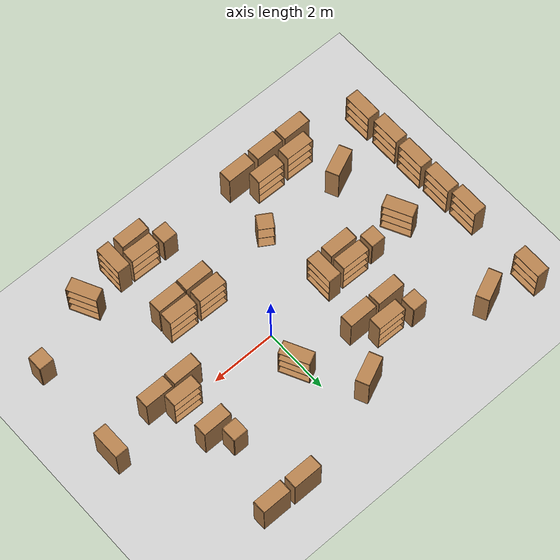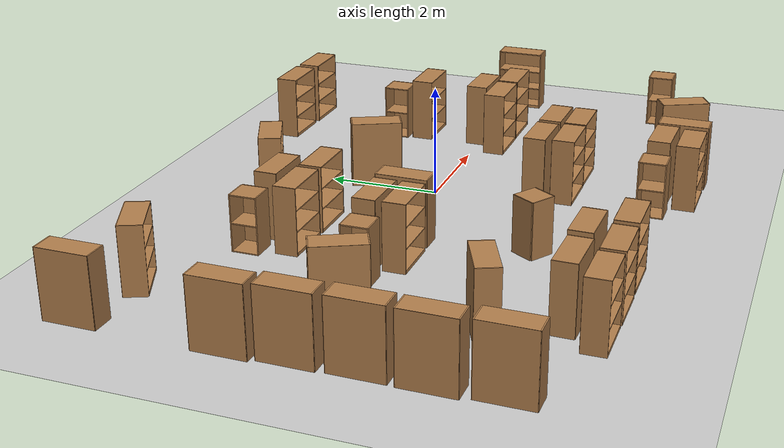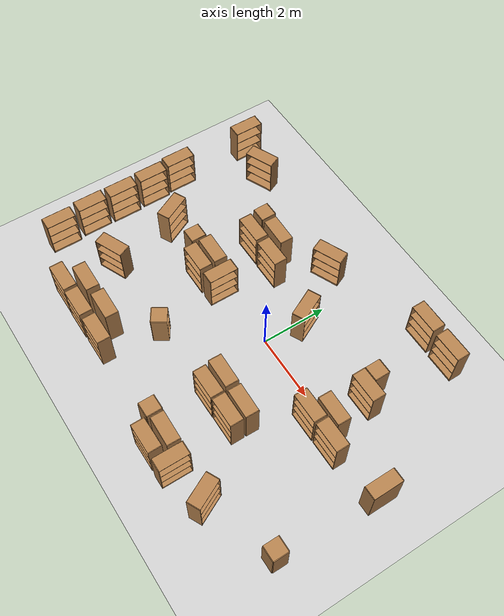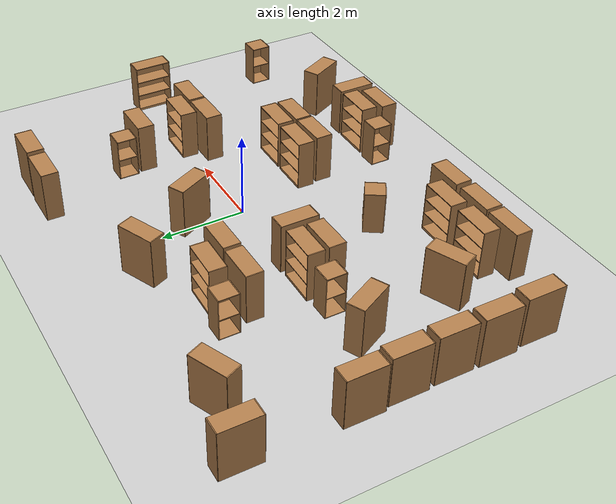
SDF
<sdf version="1.7">
 <world name="default">
  <plugin name="gazebo_ros_state" filename="libgazebo_ros_state.so">
   <ros>
    <namespace>/gazebo</namespace>
    <argument>model_states:=model_states_demo</argument>
    <argument>link_states:=link_states_demo</argument>
   </ros>
   <update_rate>1.0</update_rate>
  </plugin>
  <light name="sun" type="directional">
   <pose>0 0 10 0 -0 0</pose>
   <diffuse>0.8 0.8 0.8 1</diffuse>
   <specular>0.2 0.2 0.2 1</specular>
   <attenuation>
    <range>1000</range>
    <constant>0.9</constant>
    <linear>0.01</linear>
    <quadratic>0.001</quadratic>
   </attenuation>
   <direction>-0.5 0.1 -0.9</direction>
   <spot><inner_angle>0</inner_angle><outer_angle>0</outer_angle><falloff>0</falloff></spot>
  </light>
  <model name="ground_plane">
   <static>1</static>
   <link name="link">
    <collision name="collision">
     <geometry><plane><normal>0 0 1</normal><size>100 100</size></plane></geometry>
     <surface><friction><ode><mu>100</mu><mu2>50</mu2></ode></friction></surface>
    </collision>
    <visual name="visual">
     <cast_shadows>0</cast_shadows>
     <geometry><plane><normal>0 0 1</normal><size>100 100</size></plane></geometry>
     <material>
      <script><uri>file://media/materials/scripts/gazebo.material</uri><name>Gazebo/Grey</name></script>
     </material>
    </visual>
   </link>
  </model>
  <gravity>0 0 -9.8</gravity>
  <magnetic_field>6e-06 2.3e-05 -4.2e-05</magnetic_field>
  <atmosphere type="adiabatic"/>
  <physics type="ode">
   <max_step_size>0.001</max_step_size>
   <real_time_factor>1</real_time_factor>
   <real_time_update_rate>1000</real_time_update_rate>
  </physics>
  <scene><ambient>0.4 0.4 0.4 1</ambient><background>0.7 0.7 0.7 1</background><shadows>1</shadows></scene>
  <spherical_coordinates>
   <surface_model>EARTH_WGS84</surface_model>
   <latitude_deg>0</latitude_deg>
   <longitude_deg>0</longitude_deg>
   <elevation>0</elevation>
   <heading_deg>0</heading_deg>
  </spherical_coordinates>
  <model name="cabinet">
   <static>1</static>
   <link name="cabinet_bottom_plate">
    <inertial>
     <pose>0 0 -1 0 -0 0</pose>
     <inertia><ixx>2.05</ixx><ixy>0</ixy><ixz>0</ixz><iyy>2.05</iyy><iyz>0</iyz><izz>2.05</izz></inertia>
     <mass>25</mass>
    </inertial>
    <collision name="cabinet_bottom_plate_geom">
     <pose>0 0 0.01 0 -0 0</pose>
     <geometry><box><size>0.45 0.45 0.02</size></box></geometry>
    </collision>
    <visual name="cabinet_bottom_plate_geom_visual">
     <pose>0 0 0.01 0 -0 0</pose>
     <geometry><box><size>0.45 0.45 0.02</size></box></geometry>
     <material>
      <script><uri>file://media/materials/scripts/gazebo.material</uri><name>Gazebo/Wood</name></script>
     </material>
    </visual>
    <collision name="cabinet_bottom_plate_geom_cabinet_back_plate">
     <pose>0.235 0 0.51 0 -0 0</pose>
     <geometry><box><size>0.02 0.45 1.02</size></box></geometry>
    </collision>
    <visual name="cabinet_bottom_plate_geom_cabinet_back_plate_visual">
     <pose>0.235 0 0.51 0 -0 0</pose>
     <geometry><box><size>0.02 0.45 1.02</size></box></geometry>
     <material>
      <script><uri>file://media/materials/scripts/gazebo.material</uri><name>Gazebo/Wood</name></script>
     </material>
    </visual>
    <collision name="cabinet_bottom_plate_geom_cabinet_left_plate">
     <pose>0 0.235 0.51 0 -0 0</pose>
     <geometry><box><size>0.45 0.02 1.02</size></box></geometry>
    </collision>
    <visual name="cabinet_bottom_plate_geom_cabinet_left_plate_visual">
     <pose>0 0.235 0.51 0 -0 0</pose>
     <geometry><box><size>0.45 0.02 1.02</size></box></geometry>
     <material>
      <script><uri>file://media/materials/scripts/gazebo.material</uri><name>Gazebo/Wood</name></script>
     </material>
    </visual>
    <collision name="cabinet_bottom_plate_geom_cabinet_middle_plate">
     <pose>0 0 0.51 0 -0 0</pose>
     <geometry><box><size>0.45 0.45 0.02</size></box></geometry>
    </collision>
    <visual name="cabinet_bottom_plate_geom_cabinet_middle_plate_visual">
     <pose>0 0 0.51 0 -0 0</pose>
     <geometry><box><size>0.45 0.45 0.02</size></box></geometry>
     <material>
      <script><uri>file://media/materials/scripts/gazebo.material</uri><name>Gazebo/Wood</name></script>
     </material>
    </visual>
    <collision name="cabinet_bottom_plate_geom_cabinet_right_plate">
     <pose>0 -0.235 0.51 0 -0 0</pose>
     <geometry><box><size>0.45 0.02 1.02</size></box></geometry>
    </collision>
    <visual name="cabinet_bottom_plate_geom_cabinet_right_plate_visual">
     <pose>0 -0.235 0.51 0 -0 0</pose>
     <geometry><box><size>0.45 0.02 1.02</size></box></geometry>
     <material>
      <script><uri>file://media/materials/scripts/gazebo.material</uri><name>Gazebo/Wood</name></script>
     </material>
    </visual>
    <collision name="cabinet_bottom_plate_geom_cabinet_top_plate">
     <pose>0 0 1.01 0 -0 0</pose>
     <geometry><box><size>0.45 0.45 0.02</size></box></geometry>
    </collision>
    <visual name="cabinet_bottom_plate_geom_cabinet_top_plate_visual">
     <pose>0 0 1.01 0 -0 0</pose>
     <geometry><box><size>0.45 0.45 0.02</size></box></geometry>
     <material>
      <script><uri>file://media/materials/scripts/gazebo.material</uri><name>Gazebo/Wood</name></script>
     </material>
    </visual>
   </link>
   <pose>5.2553 -3.1844 0 0 -0 0</pose>
  </model>
  <model name="bookshelf">
   <static>1</static>
   <link name="link">
    <inertial><mass>1</mass></inertial>
    <collision name="back">
     <pose>0 0.005 0.6 0 -0 0</pose>
     <geometry><box><size>0.9 0.01 1.2</size></box></geometry>
    </collision>
    <visual name="visual1">
     <pose>0 0.005 0.6 0 -0 0</pose>
     <geometry><box><size>0.9 0.01 1.2</size></box></geometry>
     <material>
      <script><uri>file://media/materials/scripts/gazebo.material</uri><name>Gazebo/Wood</name></script>
     </material>
    </visual>
    <collision name="left_side">
     <pose>0.45 -0.195 0.6 0 -0 0</pose>
     <geometry><box><size>0.02 0.4 1.2</size></box></geometry>
    </collision>
    <visual name="visual2">
     <pose>0.45 -0.195 0.6 0 -0 0</pose>
     <geometry><box><size>0.02 0.4 1.2</size></box></geometry>
     <material>
      <script><uri>file://media/materials/scripts/gazebo.material</uri><name>Gazebo/Wood</name></script>
     </material>
    </visual>
    <collision name="right_side">
     <pose>-0.45 -0.195 0.6 0 -0 0</pose>
     <geometry><box><size>0.02 0.4 1.2</size></box></geometry>
    </collision>
    <visual name="visual3">
     <pose>-0.45 -0.195 0.6 0 -0 0</pose>
     <geometry><box><size>0.02 0.4 1.2</size></box></geometry>
     <material>
      <script><uri>file://media/materials/scripts/gazebo.material</uri><name>Gazebo/Wood</name></script>
     </material>
    </visual>
    <collision name="bottom">
     <pose>0 -0.195 0.03 0 -0 0</pose>
     <geometry><box><size>0.88 0.4 0.06</size></box></geometry>
    </collision>
    <visual name="visual4">
     <pose>0 -0.195 0.03 0 -0 0</pose>
     <geometry><box><size>0.88 0.4 0.06</size></box></geometry>
     <material>
      <script><uri>file://media/materials/scripts/gazebo.material</uri><name>Gazebo/Wood</name></script>
     </material>
    </visual>
    <collision name="top">
     <pose>0 -0.195 1.19 0 -0 0</pose>
     <geometry><box><size>0.88 0.4 0.02</size></box></geometry>
    </collision>
    <visual name="visual5">
     <pose>0 -0.195 1.19 0 -0 0</pose>
     <geometry><box><size>0.88 0.4 0.02</size></box></geometry>
     <material>
      <script><uri>file://media/materials/scripts/gazebo.material</uri><name>Gazebo/Wood</name></script>
     </material>
    </visual>
    <collision name="low_shelf">
     <pose>0 -0.195 0.43 0 -0 0</pose>
     <geometry><box><size>0.88 0.4 0.02</size></box></geometry>
    </collision>
    <visual name="visual6">
     <pose>0 -0.195 0.43 0 -0 0</pose>
     <geometry><box><size>0.88 0.4 0.02</size></box></geometry>
     <material>
      <script><uri>file://media/materials/scripts/gazebo.material</uri><name>Gazebo/Wood</name></script>
     </material>
    </visual>
    <collision name="high_shelf">
     <pose>0 -0.195 0.8 0 -0 0</pose>
     <geometry><box><size>0.88 0.4 0.02</size></box></geometry>
    </collision>
    <visual name="visual7">
     <pose>0 -0.195 0.8 0 -0 0</pose>
     <geometry><box><size>0.88 0.4 0.02</size></box></geometry>
     <material>
      <script><uri>file://media/materials/scripts/gazebo.material</uri><name>Gazebo/Wood</name></script>
     </material>
    </visual>
   </link>
   <pose>1.66773 -2.0747 0 0 -0 0</pose>
  </model>
  <model name="bookshelf_0">
   <static>1</static>
   <link name="link">
    <inertial><mass>1</mass></inertial>
    <collision name="back">
     <pose>0 0.005 0.6 0 -0 0</pose>
     <geometry><box><size>0.9 0.01 1.2</size></box></geometry>
    </collision>
    <visual name="visual1">
     <pose>0 0.005 0.6 0 -0 0</pose>
     <geometry><box><size>0.9 0.01 1.2</size></box></geometry>
     <material>
      <script><uri>file://media/materials/scripts/gazebo.material</uri><name>Gazebo/Wood</name></script>
     </material>
    </visual>
    <collision name="left_side">
     <pose>0.45 -0.195 0.6 0 -0 0</pose>
     <geometry><box><size>0.02 0.4 1.2</size></box></geometry>
    </collision>
    <visual name="visual2">
     <pose>0.45 -0.195 0.6 0 -0 0</pose>
     <geometry><box><size>0.02 0.4 1.2</size></box></geometry>
     <material>
      <script><uri>file://media/materials/scripts/gazebo.material</uri><name>Gazebo/Wood</name></script>
     </material>
    </visual>
    <collision name="right_side">
     <pose>-0.45 -0.195 0.6 0 -0 0</pose>
     <geometry><box><size>0.02 0.4 1.2</size></box></geometry>
    </collision>
    <visual name="visual3">
     <pose>-0.45 -0.195 0.6 0 -0 0</pose>
     <geometry><box><size>0.02 0.4 1.2</size></box></geometry>
     <material>
      <script><uri>file://media/materials/scripts/gazebo.material</uri><name>Gazebo/Wood</name></script>
     </material>
    </visual>
    <collision name="bottom">
     <pose>0 -0.195 0.03 0 -0 0</pose>
     <geometry><box><size>0.88 0.4 0.06</size></box></geometry>
    </collision>
    <visual name="visual4">
     <pose>0 -0.195 0.03 0 -0 0</pose>
     <geometry><box><size>0.88 0.4 0.06</size></box></geometry>
     <material>
      <script><uri>file://media/materials/scripts/gazebo.material</uri><name>Gazebo/Wood</name></script>
     </material>
    </visual>
    <collision name="top">
     <pose>0 -0.195 1.19 0 -0 0</pose>
     <geometry><box><size>0.88 0.4 0.02</size></box></geometry>
    </collision>
    <visual name="visual5">
     <pose>0 -0.195 1.19 0 -0 0</pose>
     <geometry><box><size>0.88 0.4 0.02</size></box></geometry>
     <material>
      <script><uri>file://media/materials/scripts/gazebo.material</uri><name>Gazebo/Wood</name></script>
     </material>
    </visual>
    <collision name="low_shelf">
     <pose>0 -0.195 0.43 0 -0 0</pose>
     <geometry><box><size>0.88 0.4 0.02</size></box></geometry>
    </collision>
    <visual name="visual6">
     <pose>0 -0.195 0.43 0 -0 0</pose>
     <geometry><box><size>0.88 0.4 0.02</size></box></geometry>
     <material>
      <script><uri>file://media/materials/scripts/gazebo.material</uri><name>Gazebo/Wood</name></script>
     </material>
    </visual>
    <collision name="high_shelf">
     <pose>0 -0.195 0.8 0 -0 0</pose>
     <geometry><box><size>0.88 0.4 0.02</size></box></geometry>
    </collision>
    <visual name="visual7">
     <pose>0 -0.195 0.8 0 -0 0</pose>
     <geometry><box><size>0.88 0.4 0.02</size></box></geometry>
     <material>
      <script><uri>file://media/materials/scripts/gazebo.material</uri><name>Gazebo/Wood</name></script>
     </material>
    </visual>
   </link>
   <pose>0.718779 -2.08136 0 0 -0 0</pose>
  </model>
  <model name="bookshelf_1">
   <static>1</static>
   <link name="link">
    <inertial><mass>1</mass></inertial>
    <collision name="back">
     <pose>0 0.005 0.6 0 -0 0</pose>
     <geometry><box><size>0.9 0.01 1.2</size></box></geometry>
    </collision>
    <visual name="visual1">
     <pose>0 0.005 0.6 0 -0 0</pose>
     <geometry><box><size>0.9 0.01 1.2</size></box></geometry>
     <material>
      <script><uri>file://media/materials/scripts/gazebo.material</uri><name>Gazebo/Wood</name></script>
     </material>
    </visual>
    <collision name="left_side">
     <pose>0.45 -0.195 0.6 0 -0 0</pose>
     <geometry><box><size>0.02 0.4 1.2</size></box></geometry>
    </collision>
    <visual name="visual2">
     <pose>0.45 -0.195 0.6 0 -0 0</pose>
     <geometry><box><size>0.02 0.4 1.2</size></box></geometry>
     <material>
      <script><uri>file://media/materials/scripts/gazebo.material</uri><name>Gazebo/Wood</name></script>
     </material>
    </visual>
    <collision name="right_side">
     <pose>-0.45 -0.195 0.6 0 -0 0</pose>
     <geometry><box><size>0.02 0.4 1.2</size></box></geometry>
    </collision>
    <visual name="visual3">
     <pose>-0.45 -0.195 0.6 0 -0 0</pose>
     <geometry><box><size>0.02 0.4 1.2</size></box></geometry>
     <material>
      <script><uri>file://media/materials/scripts/gazebo.material</uri><name>Gazebo/Wood</name></script>
     </material>
    </visual>
    <collision name="bottom">
     <pose>0 -0.195 0.03 0 -0 0</pose>
     <geometry><box><size>0.88 0.4 0.06</size></box></geometry>
    </collision>
    <visual name="visual4">
     <pose>0 -0.195 0.03 0 -0 0</pose>
     <geometry><box><size>0.88 0.4 0.06</size></box></geometry>
     <material>
      <script><uri>file://media/materials/scripts/gazebo.material</uri><name>Gazebo/Wood</name></script>
     </material>
    </visual>
    <collision name="top">
     <pose>0 -0.195 1.19 0 -0 0</pose>
     <geometry><box><size>0.88 0.4 0.02</size></box></geometry>
    </collision>
    <visual name="visual5">
     <pose>0 -0.195 1.19 0 -0 0</pose>
     <geometry><box><size>0.88 0.4 0.02</size></box></geometry>
     <material>
      <script><uri>file://media/materials/scripts/gazebo.material</uri><name>Gazebo/Wood</name></script>
     </material>
    </visual>
    <collision name="low_shelf">
     <pose>0 -0.195 0.43 0 -0 0</pose>
     <geometry><box><size>0.88 0.4 0.02</size></box></geometry>
    </collision>
    <visual name="visual6">
     <pose>0 -0.195 0.43 0 -0 0</pose>
     <geometry><box><size>0.88 0.4 0.02</size></box></geometry>
     <material>
      <script><uri>file://media/materials/scripts/gazebo.material</uri><name>Gazebo/Wood</name></script>
     </material>
    </visual>
    <collision name="high_shelf">
     <pose>0 -0.195 0.8 0 -0 0</pose>
     <geometry><box><size>0.88 0.4 0.02</size></box></geometry>
    </collision>
    <visual name="visual7">
     <pose>0 -0.195 0.8 0 -0 0</pose>
     <geometry><box><size>0.88 0.4 0.02</size></box></geometry>
     <material>
      <script><uri>file://media/materials/scripts/gazebo.material</uri><name>Gazebo/Wood</name></script>
     </material>
    </visual>
   </link>
   <pose>5.60417 -0.118254 0 0 0 -1.56931</pose>
  </model>
  <model name="bookshelf_1_clone">
   <static>1</static>
   <link name="link">
    <inertial><mass>1</mass></inertial>
    <collision name="back">
     <pose>0 0.005 0.6 0 -0 0</pose>
     <geometry><box><size>0.9 0.01 1.2</size></box></geometry>
    </collision>
    <visual name="visual1">
     <pose>0 0.005 0.6 0 -0 0</pose>
     <geometry><box><size>0.9 0.01 1.2</size></box></geometry>
     <material>
      <script><uri>file://media/materials/scripts/gazebo.material</uri><name>Gazebo/Wood</name></script>
     </material>
    </visual>
    <collision name="left_side">
     <pose>0.45 -0.195 0.6 0 -0 0</pose>
     <geometry><box><size>0.02 0.4 1.2</size></box></geometry>
    </collision>
    <visual name="visual2">
     <pose>0.45 -0.195 0.6 0 -0 0</pose>
     <geometry><box><size>0.02 0.4 1.2</size></box></geometry>
     <material>
      <script><uri>file://media/materials/scripts/gazebo.material</uri><name>Gazebo/Wood</name></script>
     </material>
    </visual>
    <collision name="right_side">
     <pose>-0.45 -0.195 0.6 0 -0 0</pose>
     <geometry><box><size>0.02 0.4 1.2</size></box></geometry>
    </collision>
    <visual name="visual3">
     <pose>-0.45 -0.195 0.6 0 -0 0</pose>
     <geometry><box><size>0.02 0.4 1.2</size></box></geometry>
     <material>
      <script><uri>file://media/materials/scripts/gazebo.material</uri><name>Gazebo/Wood</name></script>
     </material>
    </visual>
    <collision name="bottom">
     <pose>0 -0.195 0.03 0 -0 0</pose>
     <geometry><box><size>0.88 0.4 0.06</size></box></geometry>
    </collision>
    <visual name="visual4">
     <pose>0 -0.195 0.03 0 -0 0</pose>
     <geometry><box><size>0.88 0.4 0.06</size></box></geometry>
     <material>
      <script><uri>file://media/materials/scripts/gazebo.material</uri><name>Gazebo/Wood</name></script>
     </material>
    </visual>
    <collision name="top">
     <pose>0 -0.195 1.19 0 -0 0</pose>
     <geometry><box><size>0.88 0.4 0.02</size></box></geometry>
    </collision>
    <visual name="visual5">
     <pose>0 -0.195 1.19 0 -0 0</pose>
     <geometry><box><size>0.88 0.4 0.02</size></box></geometry>
     <material>
      <script><uri>file://media/materials/scripts/gazebo.material</uri><name>Gazebo/Wood</name></script>
     </material>
    </visual>
    <collision name="low_shelf">
     <pose>0 -0.195 0.43 0 -0 0</pose>
     <geometry><box><size>0.88 0.4 0.02</size></box></geometry>
    </collision>
    <visual name="visual6">
     <pose>0 -0.195 0.43 0 -0 0</pose>
     <geometry><box><size>0.88 0.4 0.02</size></box></geometry>
     <material>
      <script><uri>file://media/materials/scripts/gazebo.material</uri><name>Gazebo/Wood</name></script>
     </material>
    </visual>
    <collision name="high_shelf">
     <pose>0 -0.195 0.8 0 -0 0</pose>
     <geometry><box><size>0.88 0.4 0.02</size></box></geometry>
    </collision>
    <visual name="visual7">
     <pose>0 -0.195 0.8 0 -0 0</pose>
     <geometry><box><size>0.88 0.4 0.02</size></box></geometry>
     <material>
      <script><uri>file://media/materials/scripts/gazebo.material</uri><name>Gazebo/Wood</name></script>
     </material>
    </visual>
   </link>
   <pose>1.67113 -1.99457 0 0 -0 3.12003</pose>
  </model>
  <model name="bookshelf_1_clone_0">
   <static>1</static>
   <link name="link">
    <inertial><mass>1</mass></inertial>
    <collision name="back">
     <pose>0 0.005 0.6 0 -0 0</pose>
     <geometry><box><size>0.9 0.01 1.2</size></box></geometry>
    </collision>
    <visual name="visual1">
     <pose>0 0.005 0.6 0 -0 0</pose>
     <geometry><box><size>0.9 0.01 1.2</size></box></geometry>
     <material>
      <script><uri>file://media/materials/scripts/gazebo.material</uri><name>Gazebo/Wood</name></script>
     </material>
    </visual>
    <collision name="left_side">
     <pose>0.45 -0.195 0.6 0 -0 0</pose>
     <geometry><box><size>0.02 0.4 1.2</size></box></geometry>
    </collision>
    <visual name="visual2">
     <pose>0.45 -0.195 0.6 0 -0 0</pose>
     <geometry><box><size>0.02 0.4 1.2</size></box></geometry>
     <material>
      <script><uri>file://media/materials/scripts/gazebo.material</uri><name>Gazebo/Wood</name></script>
     </material>
    </visual>
    <collision name="right_side">
     <pose>-0.45 -0.195 0.6 0 -0 0</pose>
     <geometry><box><size>0.02 0.4 1.2</size></box></geometry>
    </collision>
    <visual name="visual3">
     <pose>-0.45 -0.195 0.6 0 -0 0</pose>
     <geometry><box><size>0.02 0.4 1.2</size></box></geometry>
     <material>
      <script><uri>file://media/materials/scripts/gazebo.material</uri><name>Gazebo/Wood</name></script>
     </material>
    </visual>
    <collision name="bottom">
     <pose>0 -0.195 0.03 0 -0 0</pose>
     <geometry><box><size>0.88 0.4 0.06</size></box></geometry>
    </collision>
    <visual name="visual4">
     <pose>0 -0.195 0.03 0 -0 0</pose>
     <geometry><box><size>0.88 0.4 0.06</size></box></geometry>
     <material>
      <script><uri>file://media/materials/scripts/gazebo.material</uri><name>Gazebo/Wood</name></script>
     </material>
    </visual>
    <collision name="top">
     <pose>0 -0.195 1.19 0 -0 0</pose>
     <geometry><box><size>0.88 0.4 0.02</size></box></geometry>
    </collision>
    <visual name="visual5">
     <pose>0 -0.195 1.19 0 -0 0</pose>
     <geometry><box><size>0.88 0.4 0.02</size></box></geometry>
     <material>
      <script><uri>file://media/materials/scripts/gazebo.material</uri><name>Gazebo/Wood</name></script>
     </material>
    </visual>
    <collision name="low_shelf">
     <pose>0 -0.195 0.43 0 -0 0</pose>
     <geometry><box><size>0.88 0.4 0.02</size></box></geometry>
    </collision>
    <visual name="visual6">
     <pose>0 -0.195 0.43 0 -0 0</pose>
     <geometry><box><size>0.88 0.4 0.02</size></box></geometry>
     <material>
      <script><uri>file://media/materials/scripts/gazebo.material</uri><name>Gazebo/Wood</name></script>
     </material>
    </visual>
    <collision name="high_shelf">
     <pose>0 -0.195 0.8 0 -0 0</pose>
     <geometry><box><size>0.88 0.4 0.02</size></box></geometry>
    </collision>
    <visual name="visual7">
     <pose>0 -0.195 0.8 0 -0 0</pose>
     <geometry><box><size>0.88 0.4 0.02</size></box></geometry>
     <material>
      <script><uri>file://media/materials/scripts/gazebo.material</uri><name>Gazebo/Wood</name></script>
     </material>
    </visual>
   </link>
   <pose>0.660104 -1.9707 0 0 -0 3.12003</pose>
  </model>
  <model name="bookshelf_2">
   <static>1</static>
   <link name="link">
    <inertial><mass>1</mass></inertial>
    <collision name="back">
     <pose>0 0.005 0.6 0 -0 0</pose>
     <geometry><box><size>0.9 0.01 1.2</size></box></geometry>
    </collision>
    <visual name="visual1">
     <pose>0 0.005 0.6 0 -0 0</pose>
     <geometry><box><size>0.9 0.01 1.2</size></box></geometry>
     <material>
      <script><uri>file://media/materials/scripts/gazebo.material</uri><name>Gazebo/Wood</name></script>
     </material>
    </visual>
    <collision name="left_side">
     <pose>0.45 -0.195 0.6 0 -0 0</pose>
     <geometry><box><size>0.02 0.4 1.2</size></box></geometry>
    </collision>
    <visual name="visual2">
     <pose>0.45 -0.195 0.6 0 -0 0</pose>
     <geometry><box><size>0.02 0.4 1.2</size></box></geometry>
     <material>
      <script><uri>file://media/materials/scripts/gazebo.material</uri><name>Gazebo/Wood</name></script>
     </material>
    </visual>
    <collision name="right_side">
     <pose>-0.45 -0.195 0.6 0 -0 0</pose>
     <geometry><box><size>0.02 0.4 1.2</size></box></geometry>
    </collision>
    <visual name="visual3">
     <pose>-0.45 -0.195 0.6 0 -0 0</pose>
     <geometry><box><size>0.02 0.4 1.2</size></box></geometry>
     <material>
      <script><uri>file://media/materials/scripts/gazebo.material</uri><name>Gazebo/Wood</name></script>
     </material>
    </visual>
    <collision name="bottom">
     <pose>0 -0.195 0.03 0 -0 0</pose>
     <geometry><box><size>0.88 0.4 0.06</size></box></geometry>
    </collision>
    <visual name="visual4">
     <pose>0 -0.195 0.03 0 -0 0</pose>
     <geometry><box><size>0.88 0.4 0.06</size></box></geometry>
     <material>
      <script><uri>file://media/materials/scripts/gazebo.material</uri><name>Gazebo/Wood</name></script>
     </material>
    </visual>
    <collision name="top">
     <pose>0 -0.195 1.19 0 -0 0</pose>
     <geometry><box><size>0.88 0.4 0.02</size></box></geometry>
    </collision>
    <visual name="visual5">
     <pose>0 -0.195 1.19 0 -0 0</pose>
     <geometry><box><size>0.88 0.4 0.02</size></box></geometry>
     <material>
      <script><uri>file://media/materials/scripts/gazebo.material</uri><name>Gazebo/Wood</name></script>
     </material>
    </visual>
    <collision name="low_shelf">
     <pose>0 -0.195 0.43 0 -0 0</pose>
     <geometry><box><size>0.88 0.4 0.02</size></box></geometry>
    </collision>
    <visual name="visual6">
     <pose>0 -0.195 0.43 0 -0 0</pose>
     <geometry><box><size>0.88 0.4 0.02</size></box></geometry>
     <material>
      <script><uri>file://media/materials/scripts/gazebo.material</uri><name>Gazebo/Wood</name></script>
     </material>
    </visual>
    <collision name="high_shelf">
     <pose>0 -0.195 0.8 0 -0 0</pose>
     <geometry><box><size>0.88 0.4 0.02</size></box></geometry>
    </collision>
    <visual name="visual7">
     <pose>0 -0.195 0.8 0 -0 0</pose>
     <geometry><box><size>0.88 0.4 0.02</size></box></geometry>
     <material>
      <script><uri>file://media/materials/scripts/gazebo.material</uri><name>Gazebo/Wood</name></script>
     </material>
    </visual>
   </link>
   <pose>2.71576 -0.22635 0 0 -0 0</pose>
  </model>
  <model name="bookshelf_3">
   <static>1</static>
   <link name="link">
    <inertial><mass>1</mass></inertial>
    <collision name="back">
     <pose>0 0.005 0.6 0 -0 0</pose>
     <geometry><box><size>0.9 0.01 1.2</size></box></geometry>
    </collision>
    <visual name="visual1">
     <pose>0 0.005 0.6 0 -0 0</pose>
     <geometry><box><size>0.9 0.01 1.2</size></box></geometry>
     <material>
      <script><uri>file://media/materials/scripts/gazebo.material</uri><name>Gazebo/Wood</name></script>
     </material>
    </visual>
    <collision name="left_side">
     <pose>0.45 -0.195 0.6 0 -0 0</pose>
     <geometry><box><size>0.02 0.4 1.2</size></box></geometry>
    </collision>
    <visual name="visual2">
     <pose>0.45 -0.195 0.6 0 -0 0</pose>
     <geometry><box><size>0.02 0.4 1.2</size></box></geometry>
     <material>
      <script><uri>file://media/materials/scripts/gazebo.material</uri><name>Gazebo/Wood</name></script>
     </material>
    </visual>
    <collision name="right_side">
     <pose>-0.45 -0.195 0.6 0 -0 0</pose>
     <geometry><box><size>0.02 0.4 1.2</size></box></geometry>
    </collision>
    <visual name="visual3">
     <pose>-0.45 -0.195 0.6 0 -0 0</pose>
     <geometry><box><size>0.02 0.4 1.2</size></box></geometry>
     <material>
      <script><uri>file://media/materials/scripts/gazebo.material</uri><name>Gazebo/Wood</name></script>
     </material>
    </visual>
    <collision name="bottom">
     <pose>0 -0.195 0.03 0 -0 0</pose>
     <geometry><box><size>0.88 0.4 0.06</size></box></geometry>
    </collision>
    <visual name="visual4">
     <pose>0 -0.195 0.03 0 -0 0</pose>
     <geometry><box><size>0.88 0.4 0.06</size></box></geometry>
     <material>
      <script><uri>file://media/materials/scripts/gazebo.material</uri><name>Gazebo/Wood</name></script>
     </material>
    </visual>
    <collision name="top">
     <pose>0 -0.195 1.19 0 -0 0</pose>
     <geometry><box><size>0.88 0.4 0.02</size></box></geometry>
    </collision>
    <visual name="visual5">
     <pose>0 -0.195 1.19 0 -0 0</pose>
     <geometry><box><size>0.88 0.4 0.02</size></box></geometry>
     <material>
      <script><uri>file://media/materials/scripts/gazebo.material</uri><name>Gazebo/Wood</name></script>
     </material>
    </visual>
    <collision name="low_shelf">
     <pose>0 -0.195 0.43 0 -0 0</pose>
     <geometry><box><size>0.88 0.4 0.02</size></box></geometry>
    </collision>
    <visual name="visual6">
     <pose>0 -0.195 0.43 0 -0 0</pose>
     <geometry><box><size>0.88 0.4 0.02</size></box></geometry>
     <material>
      <script><uri>file://media/materials/scripts/gazebo.material</uri><name>Gazebo/Wood</name></script>
     </material>
    </visual>
    <collision name="high_shelf">
     <pose>0 -0.195 0.8 0 -0 0</pose>
     <geometry><box><size>0.88 0.4 0.02</size></box></geometry>
    </collision>
    <visual name="visual7">
     <pose>0 -0.195 0.8 0 -0 0</pose>
     <geometry><box><size>0.88 0.4 0.02</size></box></geometry>
     <material>
      <script><uri>file://media/materials/scripts/gazebo.material</uri><name>Gazebo/Wood</name></script>
     </material>
    </visual>
   </link>
   <pose>3.67554 -0.21961 0 0 -0 0</pose>
  </model>
  <model name="bookshelf_4">
   <static>1</static>
   <link name="link">
    <inertial><mass>1</mass></inertial>
    <collision name="back">
     <pose>0 0.005 0.6 0 -0 0</pose>
     <geometry><box><size>0.9 0.01 1.2</size></box></geometry>
    </collision>
    <visual name="visual1">
     <pose>0 0.005 0.6 0 -0 0</pose>
     <geometry><box><size>0.9 0.01 1.2</size></box></geometry>
     <material>
      <script><uri>file://media/materials/scripts/gazebo.material</uri><name>Gazebo/Wood</name></script>
     </material>
    </visual>
    <collision name="left_side">
     <pose>0.45 -0.195 0.6 0 -0 0</pose>
     <geometry><box><size>0.02 0.4 1.2</size></box></geometry>
    </collision>
    <visual name="visual2">
     <pose>0.45 -0.195 0.6 0 -0 0</pose>
     <geometry><box><size>0.02 0.4 1.2</size></box></geometry>
     <material>
      <script><uri>file://media/materials/scripts/gazebo.material</uri><name>Gazebo/Wood</name></script>
     </material>
    </visual>
    <collision name="right_side">
     <pose>-0.45 -0.195 0.6 0 -0 0</pose>
     <geometry><box><size>0.02 0.4 1.2</size></box></geometry>
    </collision>
    <visual name="visual3">
     <pose>-0.45 -0.195 0.6 0 -0 0</pose>
     <geometry><box><size>0.02 0.4 1.2</size></box></geometry>
     <material>
      <script><uri>file://media/materials/scripts/gazebo.material</uri><name>Gazebo/Wood</name></script>
     </material>
    </visual>
    <collision name="bottom">
     <pose>0 -0.195 0.03 0 -0 0</pose>
     <geometry><box><size>0.88 0.4 0.06</size></box></geometry>
    </collision>
    <visual name="visual4">
     <pose>0 -0.195 0.03 0 -0 0</pose>
     <geometry><box><size>0.88 0.4 0.06</size></box></geometry>
     <material>
      <script><uri>file://media/materials/scripts/gazebo.material</uri><name>Gazebo/Wood</name></script>
     </material>
    </visual>
    <collision name="top">
     <pose>0 -0.195 1.19 0 -0 0</pose>
     <geometry><box><size>0.88 0.4 0.02</size></box></geometry>
    </collision>
    <visual name="visual5">
     <pose>0 -0.195 1.19 0 -0 0</pose>
     <geometry><box><size>0.88 0.4 0.02</size></box></geometry>
     <material>
      <script><uri>file://media/materials/scripts/gazebo.material</uri><name>Gazebo/Wood</name></script>
     </material>
    </visual>
    <collision name="low_shelf">
     <pose>0 -0.195 0.43 0 -0 0</pose>
     <geometry><box><size>0.88 0.4 0.02</size></box></geometry>
    </collision>
    <visual name="visual6">
     <pose>0 -0.195 0.43 0 -0 0</pose>
     <geometry><box><size>0.88 0.4 0.02</size></box></geometry>
     <material>
      <script><uri>file://media/materials/scripts/gazebo.material</uri><name>Gazebo/Wood</name></script>
     </material>
    </visual>
    <collision name="high_shelf">
     <pose>0 -0.195 0.8 0 -0 0</pose>
     <geometry><box><size>0.88 0.4 0.02</size></box></geometry>
    </collision>
    <visual name="visual7">
     <pose>0 -0.195 0.8 0 -0 0</pose>
     <geometry><box><size>0.88 0.4 0.02</size></box></geometry>
     <material>
      <script><uri>file://media/materials/scripts/gazebo.material</uri><name>Gazebo/Wood</name></script>
     </material>
    </visual>
   </link>
   <pose>3.06317 1.38117 0 0 -0 0</pose>
  </model>
  <model name="bookshelf_5">
   <static>1</static>
   <link name="link">
    <inertial><mass>1</mass></inertial>
    <collision name="back">
     <pose>0 0.005 0.6 0 -0 0</pose>
     <geometry><box><size>0.9 0.01 1.2</size></box></geometry>
    </collision>
    <visual name="visual1">
     <pose>0 0.005 0.6 0 -0 0</pose>
     <geometry><box><size>0.9 0.01 1.2</size></box></geometry>
     <material>
      <script><uri>file://media/materials/scripts/gazebo.material</uri><name>Gazebo/Wood</name></script>
     </material>
    </visual>
    <collision name="left_side">
     <pose>0.45 -0.195 0.6 0 -0 0</pose>
     <geometry><box><size>0.02 0.4 1.2</size></box></geometry>
    </collision>
    <visual name="visual2">
     <pose>0.45 -0.195 0.6 0 -0 0</pose>
     <geometry><box><size>0.02 0.4 1.2</size></box></geometry>
     <material>
      <script><uri>file://media/materials/scripts/gazebo.material</uri><name>Gazebo/Wood</name></script>
     </material>
    </visual>
    <collision name="right_side">
     <pose>-0.45 -0.195 0.6 0 -0 0</pose>
     <geometry><box><size>0.02 0.4 1.2</size></box></geometry>
    </collision>
    <visual name="visual3">
     <pose>-0.45 -0.195 0.6 0 -0 0</pose>
     <geometry><box><size>0.02 0.4 1.2</size></box></geometry>
     <material>
      <script><uri>file://media/materials/scripts/gazebo.material</uri><name>Gazebo/Wood</name></script>
     </material>
    </visual>
    <collision name="bottom">
     <pose>0 -0.195 0.03 0 -0 0</pose>
     <geometry><box><size>0.88 0.4 0.06</size></box></geometry>
    </collision>
    <visual name="visual4">
     <pose>0 -0.195 0.03 0 -0 0</pose>
     <geometry><box><size>0.88 0.4 0.06</size></box></geometry>
     <material>
      <script><uri>file://media/materials/scripts/gazebo.material</uri><name>Gazebo/Wood</name></script>
     </material>
    </visual>
    <collision name="top">
     <pose>0 -0.195 1.19 0 -0 0</pose>
     <geometry><box><size>0.88 0.4 0.02</size></box></geometry>
    </collision>
    <visual name="visual5">
     <pose>0 -0.195 1.19 0 -0 0</pose>
     <geometry><box><size>0.88 0.4 0.02</size></box></geometry>
     <material>
      <script><uri>file://media/materials/scripts/gazebo.material</uri><name>Gazebo/Wood</name></script>
     </material>
    </visual>
    <collision name="low_shelf">
     <pose>0 -0.195 0.43 0 -0 0</pose>
     <geometry><box><size>0.88 0.4 0.02</size></box></geometry>
    </collision>
    <visual name="visual6">
     <pose>0 -0.195 0.43 0 -0 0</pose>
     <geometry><box><size>0.88 0.4 0.02</size></box></geometry>
     <material>
      <script><uri>file://media/materials/scripts/gazebo.material</uri><name>Gazebo/Wood</name></script>
     </material>
    </visual>
    <collision name="high_shelf">
     <pose>0 -0.195 0.8 0 -0 0</pose>
     <geometry><box><size>0.88 0.4 0.02</size></box></geometry>
    </collision>
    <visual name="visual7">
     <pose>0 -0.195 0.8 0 -0 0</pose>
     <geometry><box><size>0.88 0.4 0.02</size></box></geometry>
     <material>
      <script><uri>file://media/materials/scripts/gazebo.material</uri><name>Gazebo/Wood</name></script>
     </material>
    </visual>
   </link>
   <pose>-1.83428 1.61576 0 0 -0 0</pose>
  </model>
  <model name="bookshelf_6">
   <static>1</static>
   <link name="link">
    <inertial><mass>1</mass></inertial>
    <collision name="back">
     <pose>0 0.005 0.6 0 -0 0</pose>
     <geometry><box><size>0.9 0.01 1.2</size></box></geometry>
    </collision>
    <visual name="visual1">
     <pose>0 0.005 0.6 0 -0 0</pose>
     <geometry><box><size>0.9 0.01 1.2</size></box></geometry>
     <material>
      <script><uri>file://media/materials/scripts/gazebo.material</uri><name>Gazebo/Wood</name></script>
     </material>
    </visual>
    <collision name="left_side">
     <pose>0.45 -0.195 0.6 0 -0 0</pose>
     <geometry><box><size>0.02 0.4 1.2</size></box></geometry>
    </collision>
    <visual name="visual2">
     <pose>0.45 -0.195 0.6 0 -0 0</pose>
     <geometry><box><size>0.02 0.4 1.2</size></box></geometry>
     <material>
      <script><uri>file://media/materials/scripts/gazebo.material</uri><name>Gazebo/Wood</name></script>
     </material>
    </visual>
    <collision name="right_side">
     <pose>-0.45 -0.195 0.6 0 -0 0</pose>
     <geometry><box><size>0.02 0.4 1.2</size></box></geometry>
    </collision>
    <visual name="visual3">
     <pose>-0.45 -0.195 0.6 0 -0 0</pose>
     <geometry><box><size>0.02 0.4 1.2</size></box></geometry>
     <material>
      <script><uri>file://media/materials/scripts/gazebo.material</uri><name>Gazebo/Wood</name></script>
     </material>
    </visual>
    <collision name="bottom">
     <pose>0 -0.195 0.03 0 -0 0</pose>
     <geometry><box><size>0.88 0.4 0.06</size></box></geometry>
    </collision>
    <visual name="visual4">
     <pose>0 -0.195 0.03 0 -0 0</pose>
     <geometry><box><size>0.88 0.4 0.06</size></box></geometry>
     <material>
      <script><uri>file://media/materials/scripts/gazebo.material</uri><name>Gazebo/Wood</name></script>
     </material>
    </visual>
    <collision name="top">
     <pose>0 -0.195 1.19 0 -0 0</pose>
     <geometry><box><size>0.88 0.4 0.02</size></box></geometry>
    </collision>
    <visual name="visual5">
     <pose>0 -0.195 1.19 0 -0 0</pose>
     <geometry><box><size>0.88 0.4 0.02</size></box></geometry>
     <material>
      <script><uri>file://media/materials/scripts/gazebo.material</uri><name>Gazebo/Wood</name></script>
     </material>
    </visual>
    <collision name="low_shelf">
     <pose>0 -0.195 0.43 0 -0 0</pose>
     <geometry><box><size>0.88 0.4 0.02</size></box></geometry>
    </collision>
    <visual name="visual6">
     <pose>0 -0.195 0.43 0 -0 0</pose>
     <geometry><box><size>0.88 0.4 0.02</size></box></geometry>
     <material>
      <script><uri>file://media/materials/scripts/gazebo.material</uri><name>Gazebo/Wood</name></script>
     </material>
    </visual>
    <collision name="high_shelf">
     <pose>0 -0.195 0.8 0 -0 0</pose>
     <geometry><box><size>0.88 0.4 0.02</size></box></geometry>
    </collision>
    <visual name="visual7">
     <pose>0 -0.195 0.8 0 -0 0</pose>
     <geometry><box><size>0.88 0.4 0.02</size></box></geometry>
     <material>
      <script><uri>file://media/materials/scripts/gazebo.material</uri><name>Gazebo/Wood</name></script>
     </material>
    </visual>
   </link>
   <pose>-2.82067 1.62678 0 0 -0 0</pose>
  </model>
  <model name="bookshelf_7">
   <static>1</static>
   <link name="link">
    <inertial><mass>1</mass></inertial>
    <collision name="back">
     <pose>0 0.005 0.6 0 -0 0</pose>
     <geometry><box><size>0.9 0.01 1.2</size></box></geometry>
    </collision>
    <visual name="visual1">
     <pose>0 0.005 0.6 0 -0 0</pose>
     <geometry><box><size>0.9 0.01 1.2</size></box></geometry>
     <material>
      <script><uri>file://media/materials/scripts/gazebo.material</uri><name>Gazebo/Wood</name></script>
     </material>
    </visual>
    <collision name="left_side">
     <pose>0.45 -0.195 0.6 0 -0 0</pose>
     <geometry><box><size>0.02 0.4 1.2</size></box></geometry>
    </collision>
    <visual name="visual2">
     <pose>0.45 -0.195 0.6 0 -0 0</pose>
     <geometry><box><size>0.02 0.4 1.2</size></box></geometry>
     <material>
      <script><uri>file://media/materials/scripts/gazebo.material</uri><name>Gazebo/Wood</name></script>
     </material>
    </visual>
    <collision name="right_side">
     <pose>-0.45 -0.195 0.6 0 -0 0</pose>
     <geometry><box><size>0.02 0.4 1.2</size></box></geometry>
    </collision>
    <visual name="visual3">
     <pose>-0.45 -0.195 0.6 0 -0 0</pose>
     <geometry><box><size>0.02 0.4 1.2</size></box></geometry>
     <material>
      <script><uri>file://media/materials/scripts/gazebo.material</uri><name>Gazebo/Wood</name></script>
     </material>
    </visual>
    <collision name="bottom">
     <pose>0 -0.195 0.03 0 -0 0</pose>
     <geometry><box><size>0.88 0.4 0.06</size></box></geometry>
    </collision>
    <visual name="visual4">
     <pose>0 -0.195 0.03 0 -0 0</pose>
     <geometry><box><size>0.88 0.4 0.06</size></box></geometry>
     <material>
      <script><uri>file://media/materials/scripts/gazebo.material</uri><name>Gazebo/Wood</name></script>
     </material>
    </visual>
    <collision name="top">
     <pose>0 -0.195 1.19 0 -0 0</pose>
     <geometry><box><size>0.88 0.4 0.02</size></box></geometry>
    </collision>
    <visual name="visual5">
     <pose>0 -0.195 1.19 0 -0 0</pose>
     <geometry><box><size>0.88 0.4 0.02</size></box></geometry>
     <material>
      <script><uri>file://media/materials/scripts/gazebo.material</uri><name>Gazebo/Wood</name></script>
     </material>
    </visual>
    <collision name="low_shelf">
     <pose>0 -0.195 0.43 0 -0 0</pose>
     <geometry><box><size>0.88 0.4 0.02</size></box></geometry>
    </collision>
    <visual name="visual6">
     <pose>0 -0.195 0.43 0 -0 0</pose>
     <geometry><box><size>0.88 0.4 0.02</size></box></geometry>
     <material>
      <script><uri>file://media/materials/scripts/gazebo.material</uri><name>Gazebo/Wood</name></script>
     </material>
    </visual>
    <collision name="high_shelf">
     <pose>0 -0.195 0.8 0 -0 0</pose>
     <geometry><box><size>0.88 0.4 0.02</size></box></geometry>
    </collision>
    <visual name="visual7">
     <pose>0 -0.195 0.8 0 -0 0</pose>
     <geometry><box><size>0.88 0.4 0.02</size></box></geometry>
     <material>
      <script><uri>file://media/materials/scripts/gazebo.material</uri><name>Gazebo/Wood</name></script>
     </material>
    </visual>
   </link>
   <pose>-2.82561 -0.256279 0 0 -0 0</pose>
  </model>
  <model name="bookshelf_8">
   <static>1</static>
   <link name="link">
    <inertial><mass>1</mass></inertial>
    <collision name="back">
     <pose>0 0.005 0.6 0 -0 0</pose>
     <geometry><box><size>0.9 0.01 1.2</size></box></geometry>
    </collision>
    <visual name="visual1">
     <pose>0 0.005 0.6 0 -0 0</pose>
     <geometry><box><size>0.9 0.01 1.2</size></box></geometry>
     <material>
      <script><uri>file://media/materials/scripts/gazebo.material</uri><name>Gazebo/Wood</name></script>
     </material>
    </visual>
    <collision name="left_side">
     <pose>0.45 -0.195 0.6 0 -0 0</pose>
     <geometry><box><size>0.02 0.4 1.2</size></box></geometry>
    </collision>
    <visual name="visual2">
     <pose>0.45 -0.195 0.6 0 -0 0</pose>
     <geometry><box><size>0.02 0.4 1.2</size></box></geometry>
     <material>
      <script><uri>file://media/materials/scripts/gazebo.material</uri><name>Gazebo/Wood</name></script>
     </material>
    </visual>
    <collision name="right_side">
     <pose>-0.45 -0.195 0.6 0 -0 0</pose>
     <geometry><box><size>0.02 0.4 1.2</size></box></geometry>
    </collision>
    <visual name="visual3">
     <pose>-0.45 -0.195 0.6 0 -0 0</pose>
     <geometry><box><size>0.02 0.4 1.2</size></box></geometry>
     <material>
      <script><uri>file://media/materials/scripts/gazebo.material</uri><name>Gazebo/Wood</name></script>
     </material>
    </visual>
    <collision name="bottom">
     <pose>0 -0.195 0.03 0 -0 0</pose>
     <geometry><box><size>0.88 0.4 0.06</size></box></geometry>
    </collision>
    <visual name="visual4">
     <pose>0 -0.195 0.03 0 -0 0</pose>
     <geometry><box><size>0.88 0.4 0.06</size></box></geometry>
     <material>
      <script><uri>file://media/materials/scripts/gazebo.material</uri><name>Gazebo/Wood</name></script>
     </material>
    </visual>
    <collision name="top">
     <pose>0 -0.195 1.19 0 -0 0</pose>
     <geometry><box><size>0.88 0.4 0.02</size></box></geometry>
    </collision>
    <visual name="visual5">
     <pose>0 -0.195 1.19 0 -0 0</pose>
     <geometry><box><size>0.88 0.4 0.02</size></box></geometry>
     <material>
      <script><uri>file://media/materials/scripts/gazebo.material</uri><name>Gazebo/Wood</name></script>
     </material>
    </visual>
    <collision name="low_shelf">
     <pose>0 -0.195 0.43 0 -0 0</pose>
     <geometry><box><size>0.88 0.4 0.02</size></box></geometry>
    </collision>
    <visual name="visual6">
     <pose>0 -0.195 0.43 0 -0 0</pose>
     <geometry><box><size>0.88 0.4 0.02</size></box></geometry>
     <material>
      <script><uri>file://media/materials/scripts/gazebo.material</uri><name>Gazebo/Wood</name></script>
     </material>
    </visual>
    <collision name="high_shelf">
     <pose>0 -0.195 0.8 0 -0 0</pose>
     <geometry><box><size>0.88 0.4 0.02</size></box></geometry>
    </collision>
    <visual name="visual7">
     <pose>0 -0.195 0.8 0 -0 0</pose>
     <geometry><box><size>0.88 0.4 0.02</size></box></geometry>
     <material>
      <script><uri>file://media/materials/scripts/gazebo.material</uri><name>Gazebo/Wood</name></script>
     </material>
    </visual>
   </link>
   <pose>-4.29916 -3.79165 0 0 -0 0</pose>
  </model>
  <model name="bookshelf_9">
   <static>1</static>
   <link name="link">
    <inertial><mass>1</mass></inertial>
    <collision name="back">
     <pose>0 0.005 0.6 0 -0 0</pose>
     <geometry><box><size>0.9 0.01 1.2</size></box></geometry>
    </collision>
    <visual name="visual1">
     <pose>0 0.005 0.6 0 -0 0</pose>
     <geometry><box><size>0.9 0.01 1.2</size></box></geometry>
     <material>
      <script><uri>file://media/materials/scripts/gazebo.material</uri><name>Gazebo/Wood</name></script>
     </material>
    </visual>
    <collision name="left_side">
     <pose>0.45 -0.195 0.6 0 -0 0</pose>
     <geometry><box><size>0.02 0.4 1.2</size></box></geometry>
    </collision>
    <visual name="visual2">
     <pose>0.45 -0.195 0.6 0 -0 0</pose>
     <geometry><box><size>0.02 0.4 1.2</size></box></geometry>
     <material>
      <script><uri>file://media/materials/scripts/gazebo.material</uri><name>Gazebo/Wood</name></script>
     </material>
    </visual>
    <collision name="right_side">
     <pose>-0.45 -0.195 0.6 0 -0 0</pose>
     <geometry><box><size>0.02 0.4 1.2</size></box></geometry>
    </collision>
    <visual name="visual3">
     <pose>-0.45 -0.195 0.6 0 -0 0</pose>
     <geometry><box><size>0.02 0.4 1.2</size></box></geometry>
     <material>
      <script><uri>file://media/materials/scripts/gazebo.material</uri><name>Gazebo/Wood</name></script>
     </material>
    </visual>
    <collision name="bottom">
     <pose>0 -0.195 0.03 0 -0 0</pose>
     <geometry><box><size>0.88 0.4 0.06</size></box></geometry>
    </collision>
    <visual name="visual4">
     <pose>0 -0.195 0.03 0 -0 0</pose>
     <geometry><box><size>0.88 0.4 0.06</size></box></geometry>
     <material>
      <script><uri>file://media/materials/scripts/gazebo.material</uri><name>Gazebo/Wood</name></script>
     </material>
    </visual>
    <collision name="top">
     <pose>0 -0.195 1.19 0 -0 0</pose>
     <geometry><box><size>0.88 0.4 0.02</size></box></geometry>
    </collision>
    <visual name="visual5">
     <pose>0 -0.195 1.19 0 -0 0</pose>
     <geometry><box><size>0.88 0.4 0.02</size></box></geometry>
     <material>
      <script><uri>file://media/materials/scripts/gazebo.material</uri><name>Gazebo/Wood</name></script>
     </material>
    </visual>
    <collision name="low_shelf">
     <pose>0 -0.195 0.43 0 -0 0</pose>
     <geometry><box><size>0.88 0.4 0.02</size></box></geometry>
    </collision>
    <visual name="visual6">
     <pose>0 -0.195 0.43 0 -0 0</pose>
     <geometry><box><size>0.88 0.4 0.02</size></box></geometry>
     <material>
      <script><uri>file://media/materials/scripts/gazebo.material</uri><name>Gazebo/Wood</name></script>
     </material>
    </visual>
    <collision name="high_shelf">
     <pose>0 -0.195 0.8 0 -0 0</pose>
     <geometry><box><size>0.88 0.4 0.02</size></box></geometry>
    </collision>
    <visual name="visual7">
     <pose>0 -0.195 0.8 0 -0 0</pose>
     <geometry><box><size>0.88 0.4 0.02</size></box></geometry>
     <material>
      <script><uri>file://media/materials/scripts/gazebo.material</uri><name>Gazebo/Wood</name></script>
     </material>
    </visual>
   </link>
   <pose>-3.32142 -3.80273 0 0 -0 0</pose>
  </model>
  <model name="bookshelf_10">
   <static>1</static>
   <link name="link">
    <inertial><mass>1</mass></inertial>
    <collision name="back">
     <pose>0 0.005 0.6 0 -0 0</pose>
     <geometry><box><size>0.9 0.01 1.2</size></box></geometry>
    </collision>
    <visual name="visual1">
     <pose>0 0.005 0.6 0 -0 0</pose>
     <geometry><box><size>0.9 0.01 1.2</size></box></geometry>
     <material>
      <script><uri>file://media/materials/scripts/gazebo.material</uri><name>Gazebo/Wood</name></script>
     </material>
    </visual>
    <collision name="left_side">
     <pose>0.45 -0.195 0.6 0 -0 0</pose>
     <geometry><box><size>0.02 0.4 1.2</size></box></geometry>
    </collision>
    <visual name="visual2">
     <pose>0.45 -0.195 0.6 0 -0 0</pose>
     <geometry><box><size>0.02 0.4 1.2</size></box></geometry>
     <material>
      <script><uri>file://media/materials/scripts/gazebo.material</uri><name>Gazebo/Wood</name></script>
     </material>
    </visual>
    <collision name="right_side">
     <pose>-0.45 -0.195 0.6 0 -0 0</pose>
     <geometry><box><size>0.02 0.4 1.2</size></box></geometry>
    </collision>
    <visual name="visual3">
     <pose>-0.45 -0.195 0.6 0 -0 0</pose>
     <geometry><box><size>0.02 0.4 1.2</size></box></geometry>
     <material>
      <script><uri>file://media/materials/scripts/gazebo.material</uri><name>Gazebo/Wood</name></script>
     </material>
    </visual>
    <collision name="bottom">
     <pose>0 -0.195 0.03 0 -0 0</pose>
     <geometry><box><size>0.88 0.4 0.06</size></box></geometry>
    </collision>
    <visual name="visual4">
     <pose>0 -0.195 0.03 0 -0 0</pose>
     <geometry><box><size>0.88 0.4 0.06</size></box></geometry>
     <material>
      <script><uri>file://media/materials/scripts/gazebo.material</uri><name>Gazebo/Wood</name></script>
     </material>
    </visual>
    <collision name="top">
     <pose>0 -0.195 1.19 0 -0 0</pose>
     <geometry><box><size>0.88 0.4 0.02</size></box></geometry>
    </collision>
    <visual name="visual5">
     <pose>0 -0.195 1.19 0 -0 0</pose>
     <geometry><box><size>0.88 0.4 0.02</size></box></geometry>
     <material>
      <script><uri>file://media/materials/scripts/gazebo.material</uri><name>Gazebo/Wood</name></script>
     </material>
    </visual>
    <collision name="low_shelf">
     <pose>0 -0.195 0.43 0 -0 0</pose>
     <geometry><box><size>0.88 0.4 0.02</size></box></geometry>
    </collision>
    <visual name="visual6">
     <pose>0 -0.195 0.43 0 -0 0</pose>
     <geometry><box><size>0.88 0.4 0.02</size></box></geometry>
     <material>
      <script><uri>file://media/materials/scripts/gazebo.material</uri><name>Gazebo/Wood</name></script>
     </material>
    </visual>
    <collision name="high_shelf">
     <pose>0 -0.195 0.8 0 -0 0</pose>
     <geometry><box><size>0.88 0.4 0.02</size></box></geometry>
    </collision>
    <visual name="visual7">
     <pose>0 -0.195 0.8 0 -0 0</pose>
     <geometry><box><size>0.88 0.4 0.02</size></box></geometry>
     <material>
      <script><uri>file://media/materials/scripts/gazebo.material</uri><name>Gazebo/Wood</name></script>
     </material>
    </visual>
   </link>
   <pose>-2.29001 -3.79548 0 0 -0 0</pose>
  </model>
  <model name="bookshelf_11">
   <static>1</static>
   <link name="link">
    <inertial><mass>1</mass></inertial>
    <collision name="back">
     <pose>0 0.005 0.6 0 -0 0</pose>
     <geometry><box><size>0.9 0.01 1.2</size></box></geometry>
    </collision>
    <visual name="visual1">
     <pose>0 0.005 0.6 0 -0 0</pose>
     <geometry><box><size>0.9 0.01 1.2</size></box></geometry>
     <material>
      <script><uri>file://media/materials/scripts/gazebo.material</uri><name>Gazebo/Wood</name></script>
     </material>
    </visual>
    <collision name="left_side">
     <pose>0.45 -0.195 0.6 0 -0 0</pose>
     <geometry><box><size>0.02 0.4 1.2</size></box></geometry>
    </collision>
    <visual name="visual2">
     <pose>0.45 -0.195 0.6 0 -0 0</pose>
     <geometry><box><size>0.02 0.4 1.2</size></box></geometry>
     <material>
      <script><uri>file://media/materials/scripts/gazebo.material</uri><name>Gazebo/Wood</name></script>
     </material>
    </visual>
    <collision name="right_side">
     <pose>-0.45 -0.195 0.6 0 -0 0</pose>
     <geometry><box><size>0.02 0.4 1.2</size></box></geometry>
    </collision>
    <visual name="visual3">
     <pose>-0.45 -0.195 0.6 0 -0 0</pose>
     <geometry><box><size>0.02 0.4 1.2</size></box></geometry>
     <material>
      <script><uri>file://media/materials/scripts/gazebo.material</uri><name>Gazebo/Wood</name></script>
     </material>
    </visual>
    <collision name="bottom">
     <pose>0 -0.195 0.03 0 -0 0</pose>
     <geometry><box><size>0.88 0.4 0.06</size></box></geometry>
    </collision>
    <visual name="visual4">
     <pose>0 -0.195 0.03 0 -0 0</pose>
     <geometry><box><size>0.88 0.4 0.06</size></box></geometry>
     <material>
      <script><uri>file://media/materials/scripts/gazebo.material</uri><name>Gazebo/Wood</name></script>
     </material>
    </visual>
    <collision name="top">
     <pose>0 -0.195 1.19 0 -0 0</pose>
     <geometry><box><size>0.88 0.4 0.02</size></box></geometry>
    </collision>
    <visual name="visual5">
     <pose>0 -0.195 1.19 0 -0 0</pose>
     <geometry><box><size>0.88 0.4 0.02</size></box></geometry>
     <material>
      <script><uri>file://media/materials/scripts/gazebo.material</uri><name>Gazebo/Wood</name></script>
     </material>
    </visual>
    <collision name="low_shelf">
     <pose>0 -0.195 0.43 0 -0 0</pose>
     <geometry><box><size>0.88 0.4 0.02</size></box></geometry>
    </collision>
    <visual name="visual6">
     <pose>0 -0.195 0.43 0 -0 0</pose>
     <geometry><box><size>0.88 0.4 0.02</size></box></geometry>
     <material>
      <script><uri>file://media/materials/scripts/gazebo.material</uri><name>Gazebo/Wood</name></script>
     </material>
    </visual>
    <collision name="high_shelf">
     <pose>0 -0.195 0.8 0 -0 0</pose>
     <geometry><box><size>0.88 0.4 0.02</size></box></geometry>
    </collision>
    <visual name="visual7">
     <pose>0 -0.195 0.8 0 -0 0</pose>
     <geometry><box><size>0.88 0.4 0.02</size></box></geometry>
     <material>
      <script><uri>file://media/materials/scripts/gazebo.material</uri><name>Gazebo/Wood</name></script>
     </material>
    </visual>
   </link>
   <pose>1.16592 -4.18389 0 0 -0 0</pose>
  </model>
  <model name="bookshelf_12">
   <static>1</static>
   <link name="link">
    <inertial><mass>1</mass></inertial>
    <collision name="back">
     <pose>0 0.005 0.6 0 -0 0</pose>
     <geometry><box><size>0.9 0.01 1.2</size></box></geometry>
    </collision>
    <visual name="visual1">
     <pose>0 0.005 0.6 0 -0 0</pose>
     <geometry><box><size>0.9 0.01 1.2</size></box></geometry>
     <material>
      <script><uri>file://media/materials/scripts/gazebo.material</uri><name>Gazebo/Wood</name></script>
     </material>
    </visual>
    <collision name="left_side">
     <pose>0.45 -0.195 0.6 0 -0 0</pose>
     <geometry><box><size>0.02 0.4 1.2</size></box></geometry>
    </collision>
    <visual name="visual2">
     <pose>0.45 -0.195 0.6 0 -0 0</pose>
     <geometry><box><size>0.02 0.4 1.2</size></box></geometry>
     <material>
      <script><uri>file://media/materials/scripts/gazebo.material</uri><name>Gazebo/Wood</name></script>
     </material>
    </visual>
    <collision name="right_side">
     <pose>-0.45 -0.195 0.6 0 -0 0</pose>
     <geometry><box><size>0.02 0.4 1.2</size></box></geometry>
    </collision>
    <visual name="visual3">
     <pose>-0.45 -0.195 0.6 0 -0 0</pose>
     <geometry><box><size>0.02 0.4 1.2</size></box></geometry>
     <material>
      <script><uri>file://media/materials/scripts/gazebo.material</uri><name>Gazebo/Wood</name></script>
     </material>
    </visual>
    <collision name="bottom">
     <pose>0 -0.195 0.03 0 -0 0</pose>
     <geometry><box><size>0.88 0.4 0.06</size></box></geometry>
    </collision>
    <visual name="visual4">
     <pose>0 -0.195 0.03 0 -0 0</pose>
     <geometry><box><size>0.88 0.4 0.06</size></box></geometry>
     <material>
      <script><uri>file://media/materials/scripts/gazebo.material</uri><name>Gazebo/Wood</name></script>
     </material>
    </visual>
    <collision name="top">
     <pose>0 -0.195 1.19 0 -0 0</pose>
     <geometry><box><size>0.88 0.4 0.02</size></box></geometry>
    </collision>
    <visual name="visual5">
     <pose>0 -0.195 1.19 0 -0 0</pose>
     <geometry><box><size>0.88 0.4 0.02</size></box></geometry>
     <material>
      <script><uri>file://media/materials/scripts/gazebo.material</uri><name>Gazebo/Wood</name></script>
     </material>
    </visual>
    <collision name="low_shelf">
     <pose>0 -0.195 0.43 0 -0 0</pose>
     <geometry><box><size>0.88 0.4 0.02</size></box></geometry>
    </collision>
    <visual name="visual6">
     <pose>0 -0.195 0.43 0 -0 0</pose>
     <geometry><box><size>0.88 0.4 0.02</size></box></geometry>
     <material>
      <script><uri>file://media/materials/scripts/gazebo.material</uri><name>Gazebo/Wood</name></script>
     </material>
    </visual>
    <collision name="high_shelf">
     <pose>0 -0.195 0.8 0 -0 0</pose>
     <geometry><box><size>0.88 0.4 0.02</size></box></geometry>
    </collision>
    <visual name="visual7">
     <pose>0 -0.195 0.8 0 -0 0</pose>
     <geometry><box><size>0.88 0.4 0.02</size></box></geometry>
     <material>
      <script><uri>file://media/materials/scripts/gazebo.material</uri><name>Gazebo/Wood</name></script>
     </material>
    </visual>
   </link>
   <pose>3.32228 3.98277 0 0 -0 0</pose>
  </model>
  <model name="bookshelf_13">
   <static>1</static>
   <link name="link">
    <inertial><mass>1</mass></inertial>
    <collision name="back">
     <pose>0 0.005 0.6 0 -0 0</pose>
     <geometry><box><size>0.9 0.01 1.2</size></box></geometry>
    </collision>
    <visual name="visual1">
     <pose>0 0.005 0.6 0 -0 0</pose>
     <geometry><box><size>0.9 0.01 1.2</size></box></geometry>
     <material>
      <script><uri>file://media/materials/scripts/gazebo.material</uri><name>Gazebo/Wood</name></script>
     </material>
    </visual>
    <collision name="left_side">
     <pose>0.45 -0.195 0.6 0 -0 0</pose>
     <geometry><box><size>0.02 0.4 1.2</size></box></geometry>
    </collision>
    <visual name="visual2">
     <pose>0.45 -0.195 0.6 0 -0 0</pose>
     <geometry><box><size>0.02 0.4 1.2</size></box></geometry>
     <material>
      <script><uri>file://media/materials/scripts/gazebo.material</uri><name>Gazebo/Wood</name></script>
     </material>
    </visual>
    <collision name="right_side">
     <pose>-0.45 -0.195 0.6 0 -0 0</pose>
     <geometry><box><size>0.02 0.4 1.2</size></box></geometry>
    </collision>
    <visual name="visual3">
     <pose>-0.45 -0.195 0.6 0 -0 0</pose>
     <geometry><box><size>0.02 0.4 1.2</size></box></geometry>
     <material>
      <script><uri>file://media/materials/scripts/gazebo.material</uri><name>Gazebo/Wood</name></script>
     </material>
    </visual>
    <collision name="bottom">
     <pose>0 -0.195 0.03 0 -0 0</pose>
     <geometry><box><size>0.88 0.4 0.06</size></box></geometry>
    </collision>
    <visual name="visual4">
     <pose>0 -0.195 0.03 0 -0 0</pose>
     <geometry><box><size>0.88 0.4 0.06</size></box></geometry>
     <material>
      <script><uri>file://media/materials/scripts/gazebo.material</uri><name>Gazebo/Wood</name></script>
     </material>
    </visual>
    <collision name="top">
     <pose>0 -0.195 1.19 0 -0 0</pose>
     <geometry><box><size>0.88 0.4 0.02</size></box></geometry>
    </collision>
    <visual name="visual5">
     <pose>0 -0.195 1.19 0 -0 0</pose>
     <geometry><box><size>0.88 0.4 0.02</size></box></geometry>
     <material>
      <script><uri>file://media/materials/scripts/gazebo.material</uri><name>Gazebo/Wood</name></script>
     </material>
    </visual>
    <collision name="low_shelf">
     <pose>0 -0.195 0.43 0 -0 0</pose>
     <geometry><box><size>0.88 0.4 0.02</size></box></geometry>
    </collision>
    <visual name="visual6">
     <pose>0 -0.195 0.43 0 -0 0</pose>
     <geometry><box><size>0.88 0.4 0.02</size></box></geometry>
     <material>
      <script><uri>file://media/materials/scripts/gazebo.material</uri><name>Gazebo/Wood</name></script>
     </material>
    </visual>
    <collision name="high_shelf">
     <pose>0 -0.195 0.8 0 -0 0</pose>
     <geometry><box><size>0.88 0.4 0.02</size></box></geometry>
    </collision>
    <visual name="visual7">
     <pose>0 -0.195 0.8 0 -0 0</pose>
     <geometry><box><size>0.88 0.4 0.02</size></box></geometry>
     <material>
      <script><uri>file://media/materials/scripts/gazebo.material</uri><name>Gazebo/Wood</name></script>
     </material>
    </visual>
   </link>
   <pose>2.28216 4.00236 0 0 -0 0</pose>
  </model>
  <model name="bookshelf_1_clone_clone">
   <static>1</static>
   <link name="link">
    <inertial><mass>1</mass></inertial>
    <collision name="back">
     <pose>0 0.005 0.6 0 -0 0</pose>
     <geometry><box><size>0.9 0.01 1.2</size></box></geometry>
    </collision>
    <visual name="visual1">
     <pose>0 0.005 0.6 0 -0 0</pose>
     <geometry><box><size>0.9 0.01 1.2</size></box></geometry>
     <material>
      <script><uri>file://media/materials/scripts/gazebo.material</uri><name>Gazebo/Wood</name></script>
     </material>
    </visual>
    <collision name="left_side">
     <pose>0.45 -0.195 0.6 0 -0 0</pose>
     <geometry><box><size>0.02 0.4 1.2</size></box></geometry>
    </collision>
    <visual name="visual2">
     <pose>0.45 -0.195 0.6 0 -0 0</pose>
     <geometry><box><size>0.02 0.4 1.2</size></box></geometry>
     <material>
      <script><uri>file://media/materials/scripts/gazebo.material</uri><name>Gazebo/Wood</name></script>
     </material>
    </visual>
    <collision name="right_side">
     <pose>-0.45 -0.195 0.6 0 -0 0</pose>
     <geometry><box><size>0.02 0.4 1.2</size></box></geometry>
    </collision>
    <visual name="visual3">
     <pose>-0.45 -0.195 0.6 0 -0 0</pose>
     <geometry><box><size>0.02 0.4 1.2</size></box></geometry>
     <material>
      <script><uri>file://media/materials/scripts/gazebo.material</uri><name>Gazebo/Wood</name></script>
     </material>
    </visual>
    <collision name="bottom">
     <pose>0 -0.195 0.03 0 -0 0</pose>
     <geometry><box><size>0.88 0.4 0.06</size></box></geometry>
    </collision>
    <visual name="visual4">
     <pose>0 -0.195 0.03 0 -0 0</pose>
     <geometry><box><size>0.88 0.4 0.06</size></box></geometry>
     <material>
      <script><uri>file://media/materials/scripts/gazebo.material</uri><name>Gazebo/Wood</name></script>
     </material>
    </visual>
    <collision name="top">
     <pose>0 -0.195 1.19 0 -0 0</pose>
     <geometry><box><size>0.88 0.4 0.02</size></box></geometry>
    </collision>
    <visual name="visual5">
     <pose>0 -0.195 1.19 0 -0 0</pose>
     <geometry><box><size>0.88 0.4 0.02</size></box></geometry>
     <material>
      <script><uri>file://media/materials/scripts/gazebo.material</uri><name>Gazebo/Wood</name></script>
     </material>
    </visual>
    <collision name="low_shelf">
     <pose>0 -0.195 0.43 0 -0 0</pose>
     <geometry><box><size>0.88 0.4 0.02</size></box></geometry>
    </collision>
    <visual name="visual6">
     <pose>0 -0.195 0.43 0 -0 0</pose>
     <geometry><box><size>0.88 0.4 0.02</size></box></geometry>
     <material>
      <script><uri>file://media/materials/scripts/gazebo.material</uri><name>Gazebo/Wood</name></script>
     </material>
    </visual>
    <collision name="high_shelf">
     <pose>0 -0.195 0.8 0 -0 0</pose>
     <geometry><box><size>0.88 0.4 0.02</size></box></geometry>
    </collision>
    <visual name="visual7">
     <pose>0 -0.195 0.8 0 -0 0</pose>
     <geometry><box><size>0.88 0.4 0.02</size></box></geometry>
     <material>
      <script><uri>file://media/materials/scripts/gazebo.material</uri><name>Gazebo/Wood</name></script>
     </material>
    </visual>
   </link>
   <pose>-2.87424 -3.6202 0 0 -0 3.12003</pose>
  </model>
  <model name="bookshelf_1_clone_clone_0">
   <static>1</static>
   <link name="link">
    <inertial><mass>1</mass></inertial>
    <collision name="back">
     <pose>0 0.005 0.6 0 -0 0</pose>
     <geometry><box><size>0.9 0.01 1.2</size></box></geometry>
    </collision>
    <visual name="visual1">
     <pose>0 0.005 0.6 0 -0 0</pose>
     <geometry><box><size>0.9 0.01 1.2</size></box></geometry>
     <material>
      <script><uri>file://media/materials/scripts/gazebo.material</uri><name>Gazebo/Wood</name></script>
     </material>
    </visual>
    <collision name="left_side">
     <pose>0.45 -0.195 0.6 0 -0 0</pose>
     <geometry><box><size>0.02 0.4 1.2</size></box></geometry>
    </collision>
    <visual name="visual2">
     <pose>0.45 -0.195 0.6 0 -0 0</pose>
     <geometry><box><size>0.02 0.4 1.2</size></box></geometry>
     <material>
      <script><uri>file://media/materials/scripts/gazebo.material</uri><name>Gazebo/Wood</name></script>
     </material>
    </visual>
    <collision name="right_side">
     <pose>-0.45 -0.195 0.6 0 -0 0</pose>
     <geometry><box><size>0.02 0.4 1.2</size></box></geometry>
    </collision>
    <visual name="visual3">
     <pose>-0.45 -0.195 0.6 0 -0 0</pose>
     <geometry><box><size>0.02 0.4 1.2</size></box></geometry>
     <material>
      <script><uri>file://media/materials/scripts/gazebo.material</uri><name>Gazebo/Wood</name></script>
     </material>
    </visual>
    <collision name="bottom">
     <pose>0 -0.195 0.03 0 -0 0</pose>
     <geometry><box><size>0.88 0.4 0.06</size></box></geometry>
    </collision>
    <visual name="visual4">
     <pose>0 -0.195 0.03 0 -0 0</pose>
     <geometry><box><size>0.88 0.4 0.06</size></box></geometry>
     <material>
      <script><uri>file://media/materials/scripts/gazebo.material</uri><name>Gazebo/Wood</name></script>
     </material>
    </visual>
    <collision name="top">
     <pose>0 -0.195 1.19 0 -0 0</pose>
     <geometry><box><size>0.88 0.4 0.02</size></box></geometry>
    </collision>
    <visual name="visual5">
     <pose>0 -0.195 1.19 0 -0 0</pose>
     <geometry><box><size>0.88 0.4 0.02</size></box></geometry>
     <material>
      <script><uri>file://media/materials/scripts/gazebo.material</uri><name>Gazebo/Wood</name></script>
     </material>
    </visual>
    <collision name="low_shelf">
     <pose>0 -0.195 0.43 0 -0 0</pose>
     <geometry><box><size>0.88 0.4 0.02</size></box></geometry>
    </collision>
    <visual name="visual6">
     <pose>0 -0.195 0.43 0 -0 0</pose>
     <geometry><box><size>0.88 0.4 0.02</size></box></geometry>
     <material>
      <script><uri>file://media/materials/scripts/gazebo.material</uri><name>Gazebo/Wood</name></script>
     </material>
    </visual>
    <collision name="high_shelf">
     <pose>0 -0.195 0.8 0 -0 0</pose>
     <geometry><box><size>0.88 0.4 0.02</size></box></geometry>
    </collision>
    <visual name="visual7">
     <pose>0 -0.195 0.8 0 -0 0</pose>
     <geometry><box><size>0.88 0.4 0.02</size></box></geometry>
     <material>
      <script><uri>file://media/materials/scripts/gazebo.material</uri><name>Gazebo/Wood</name></script>
     </material>
    </visual>
   </link>
   <pose>-3.95037 -3.64569 0 0 -0 3.12003</pose>
  </model>
  <model name="bookshelf_1_clone_clone_1">
   <static>1</static>
   <link name="link">
    <inertial><mass>1</mass></inertial>
    <collision name="back">
     <pose>0 0.005 0.6 0 -0 0</pose>
     <geometry><box><size>0.9 0.01 1.2</size></box></geometry>
    </collision>
    <visual name="visual1">
     <pose>0 0.005 0.6 0 -0 0</pose>
     <geometry><box><size>0.9 0.01 1.2</size></box></geometry>
     <material>
      <script><uri>file://media/materials/scripts/gazebo.material</uri><name>Gazebo/Wood</name></script>
     </material>
    </visual>
    <collision name="left_side">
     <pose>0.45 -0.195 0.6 0 -0 0</pose>
     <geometry><box><size>0.02 0.4 1.2</size></box></geometry>
    </collision>
    <visual name="visual2">
     <pose>0.45 -0.195 0.6 0 -0 0</pose>
     <geometry><box><size>0.02 0.4 1.2</size></box></geometry>
     <material>
      <script><uri>file://media/materials/scripts/gazebo.material</uri><name>Gazebo/Wood</name></script>
     </material>
    </visual>
    <collision name="right_side">
     <pose>-0.45 -0.195 0.6 0 -0 0</pose>
     <geometry><box><size>0.02 0.4 1.2</size></box></geometry>
    </collision>
    <visual name="visual3">
     <pose>-0.45 -0.195 0.6 0 -0 0</pose>
     <geometry><box><size>0.02 0.4 1.2</size></box></geometry>
     <material>
      <script><uri>file://media/materials/scripts/gazebo.material</uri><name>Gazebo/Wood</name></script>
     </material>
    </visual>
    <collision name="bottom">
     <pose>0 -0.195 0.03 0 -0 0</pose>
     <geometry><box><size>0.88 0.4 0.06</size></box></geometry>
    </collision>
    <visual name="visual4">
     <pose>0 -0.195 0.03 0 -0 0</pose>
     <geometry><box><size>0.88 0.4 0.06</size></box></geometry>
     <material>
      <script><uri>file://media/materials/scripts/gazebo.material</uri><name>Gazebo/Wood</name></script>
     </material>
    </visual>
    <collision name="top">
     <pose>0 -0.195 1.19 0 -0 0</pose>
     <geometry><box><size>0.88 0.4 0.02</size></box></geometry>
    </collision>
    <visual name="visual5">
     <pose>0 -0.195 1.19 0 -0 0</pose>
     <geometry><box><size>0.88 0.4 0.02</size></box></geometry>
     <material>
      <script><uri>file://media/materials/scripts/gazebo.material</uri><name>Gazebo/Wood</name></script>
     </material>
    </visual>
    <collision name="low_shelf">
     <pose>0 -0.195 0.43 0 -0 0</pose>
     <geometry><box><size>0.88 0.4 0.02</size></box></geometry>
    </collision>
    <visual name="visual6">
     <pose>0 -0.195 0.43 0 -0 0</pose>
     <geometry><box><size>0.88 0.4 0.02</size></box></geometry>
     <material>
      <script><uri>file://media/materials/scripts/gazebo.material</uri><name>Gazebo/Wood</name></script>
     </material>
    </visual>
    <collision name="high_shelf">
     <pose>0 -0.195 0.8 0 -0 0</pose>
     <geometry><box><size>0.88 0.4 0.02</size></box></geometry>
    </collision>
    <visual name="visual7">
     <pose>0 -0.195 0.8 0 -0 0</pose>
     <geometry><box><size>0.88 0.4 0.02</size></box></geometry>
     <material>
      <script><uri>file://media/materials/scripts/gazebo.material</uri><name>Gazebo/Wood</name></script>
     </material>
    </visual>
   </link>
   <pose>-2.83533 -0.148738 0 0 -0 3.12003</pose>
  </model>
  <model name="bookshelf_1_clone_clone_2">
   <static>1</static>
   <link name="link">
    <inertial><mass>1</mass></inertial>
    <collision name="back">
     <pose>0 0.005 0.6 0 -0 0</pose>
     <geometry><box><size>0.9 0.01 1.2</size></box></geometry>
    </collision>
    <visual name="visual1">
     <pose>0 0.005 0.6 0 -0 0</pose>
     <geometry><box><size>0.9 0.01 1.2</size></box></geometry>
     <material>
      <script><uri>file://media/materials/scripts/gazebo.material</uri><name>Gazebo/Wood</name></script>
     </material>
    </visual>
    <collision name="left_side">
     <pose>0.45 -0.195 0.6 0 -0 0</pose>
     <geometry><box><size>0.02 0.4 1.2</size></box></geometry>
    </collision>
    <visual name="visual2">
     <pose>0.45 -0.195 0.6 0 -0 0</pose>
     <geometry><box><size>0.02 0.4 1.2</size></box></geometry>
     <material>
      <script><uri>file://media/materials/scripts/gazebo.material</uri><name>Gazebo/Wood</name></script>
     </material>
    </visual>
    <collision name="right_side">
     <pose>-0.45 -0.195 0.6 0 -0 0</pose>
     <geometry><box><size>0.02 0.4 1.2</size></box></geometry>
    </collision>
    <visual name="visual3">
     <pose>-0.45 -0.195 0.6 0 -0 0</pose>
     <geometry><box><size>0.02 0.4 1.2</size></box></geometry>
     <material>
      <script><uri>file://media/materials/scripts/gazebo.material</uri><name>Gazebo/Wood</name></script>
     </material>
    </visual>
    <collision name="bottom">
     <pose>0 -0.195 0.03 0 -0 0</pose>
     <geometry><box><size>0.88 0.4 0.06</size></box></geometry>
    </collision>
    <visual name="visual4">
     <pose>0 -0.195 0.03 0 -0 0</pose>
     <geometry><box><size>0.88 0.4 0.06</size></box></geometry>
     <material>
      <script><uri>file://media/materials/scripts/gazebo.material</uri><name>Gazebo/Wood</name></script>
     </material>
    </visual>
    <collision name="top">
     <pose>0 -0.195 1.19 0 -0 0</pose>
     <geometry><box><size>0.88 0.4 0.02</size></box></geometry>
    </collision>
    <visual name="visual5">
     <pose>0 -0.195 1.19 0 -0 0</pose>
     <geometry><box><size>0.88 0.4 0.02</size></box></geometry>
     <material>
      <script><uri>file://media/materials/scripts/gazebo.material</uri><name>Gazebo/Wood</name></script>
     </material>
    </visual>
    <collision name="low_shelf">
     <pose>0 -0.195 0.43 0 -0 0</pose>
     <geometry><box><size>0.88 0.4 0.02</size></box></geometry>
    </collision>
    <visual name="visual6">
     <pose>0 -0.195 0.43 0 -0 0</pose>
     <geometry><box><size>0.88 0.4 0.02</size></box></geometry>
     <material>
      <script><uri>file://media/materials/scripts/gazebo.material</uri><name>Gazebo/Wood</name></script>
     </material>
    </visual>
    <collision name="high_shelf">
     <pose>0 -0.195 0.8 0 -0 0</pose>
     <geometry><box><size>0.88 0.4 0.02</size></box></geometry>
    </collision>
    <visual name="visual7">
     <pose>0 -0.195 0.8 0 -0 0</pose>
     <geometry><box><size>0.88 0.4 0.02</size></box></geometry>
     <material>
      <script><uri>file://media/materials/scripts/gazebo.material</uri><name>Gazebo/Wood</name></script>
     </material>
    </visual>
   </link>
   <pose>3.11001 -0.142867 0 0 -0 3.12003</pose>
  </model>
  <model name="bookshelf_1_clone_clone_3">
   <static>1</static>
   <link name="link">
    <inertial><mass>1</mass></inertial>
    <collision name="back">
     <pose>0 0.005 0.6 0 -0 0</pose>
     <geometry><box><size>0.9 0.01 1.2</size></box></geometry>
    </collision>
    <visual name="visual1">
     <pose>0 0.005 0.6 0 -0 0</pose>
     <geometry><box><size>0.9 0.01 1.2</size></box></geometry>
     <material>
      <script><uri>file://media/materials/scripts/gazebo.material</uri><name>Gazebo/Wood</name></script>
     </material>
    </visual>
    <collision name="left_side">
     <pose>0.45 -0.195 0.6 0 -0 0</pose>
     <geometry><box><size>0.02 0.4 1.2</size></box></geometry>
    </collision>
    <visual name="visual2">
     <pose>0.45 -0.195 0.6 0 -0 0</pose>
     <geometry><box><size>0.02 0.4 1.2</size></box></geometry>
     <material>
      <script><uri>file://media/materials/scripts/gazebo.material</uri><name>Gazebo/Wood</name></script>
     </material>
    </visual>
    <collision name="right_side">
     <pose>-0.45 -0.195 0.6 0 -0 0</pose>
     <geometry><box><size>0.02 0.4 1.2</size></box></geometry>
    </collision>
    <visual name="visual3">
     <pose>-0.45 -0.195 0.6 0 -0 0</pose>
     <geometry><box><size>0.02 0.4 1.2</size></box></geometry>
     <material>
      <script><uri>file://media/materials/scripts/gazebo.material</uri><name>Gazebo/Wood</name></script>
     </material>
    </visual>
    <collision name="bottom">
     <pose>0 -0.195 0.03 0 -0 0</pose>
     <geometry><box><size>0.88 0.4 0.06</size></box></geometry>
    </collision>
    <visual name="visual4">
     <pose>0 -0.195 0.03 0 -0 0</pose>
     <geometry><box><size>0.88 0.4 0.06</size></box></geometry>
     <material>
      <script><uri>file://media/materials/scripts/gazebo.material</uri><name>Gazebo/Wood</name></script>
     </material>
    </visual>
    <collision name="top">
     <pose>0 -0.195 1.19 0 -0 0</pose>
     <geometry><box><size>0.88 0.4 0.02</size></box></geometry>
    </collision>
    <visual name="visual5">
     <pose>0 -0.195 1.19 0 -0 0</pose>
     <geometry><box><size>0.88 0.4 0.02</size></box></geometry>
     <material>
      <script><uri>file://media/materials/scripts/gazebo.material</uri><name>Gazebo/Wood</name></script>
     </material>
    </visual>
    <collision name="low_shelf">
     <pose>0 -0.195 0.43 0 -0 0</pose>
     <geometry><box><size>0.88 0.4 0.02</size></box></geometry>
    </collision>
    <visual name="visual6">
     <pose>0 -0.195 0.43 0 -0 0</pose>
     <geometry><box><size>0.88 0.4 0.02</size></box></geometry>
     <material>
      <script><uri>file://media/materials/scripts/gazebo.material</uri><name>Gazebo/Wood</name></script>
     </material>
    </visual>
    <collision name="high_shelf">
     <pose>0 -0.195 0.8 0 -0 0</pose>
     <geometry><box><size>0.88 0.4 0.02</size></box></geometry>
    </collision>
    <visual name="visual7">
     <pose>0 -0.195 0.8 0 -0 0</pose>
     <geometry><box><size>0.88 0.4 0.02</size></box></geometry>
     <material>
      <script><uri>file://media/materials/scripts/gazebo.material</uri><name>Gazebo/Wood</name></script>
     </material>
    </visual>
   </link>
   <pose>1.24582 -4.06672 0 0 -0 3.12003</pose>
  </model>
  <model name="bookshelf_1_clone_clone_4">
   <static>1</static>
   <link name="link">
    <inertial><mass>1</mass></inertial>
    <collision name="back">
     <pose>0 0.005 0.6 0 -0 0</pose>
     <geometry><box><size>0.9 0.01 1.2</size></box></geometry>
    </collision>
    <visual name="visual1">
     <pose>0 0.005 0.6 0 -0 0</pose>
     <geometry><box><size>0.9 0.01 1.2</size></box></geometry>
     <material>
      <script><uri>file://media/materials/scripts/gazebo.material</uri><name>Gazebo/Wood</name></script>
     </material>
    </visual>
    <collision name="left_side">
     <pose>0.45 -0.195 0.6 0 -0 0</pose>
     <geometry><box><size>0.02 0.4 1.2</size></box></geometry>
    </collision>
    <visual name="visual2">
     <pose>0.45 -0.195 0.6 0 -0 0</pose>
     <geometry><box><size>0.02 0.4 1.2</size></box></geometry>
     <material>
      <script><uri>file://media/materials/scripts/gazebo.material</uri><name>Gazebo/Wood</name></script>
     </material>
    </visual>
    <collision name="right_side">
     <pose>-0.45 -0.195 0.6 0 -0 0</pose>
     <geometry><box><size>0.02 0.4 1.2</size></box></geometry>
    </collision>
    <visual name="visual3">
     <pose>-0.45 -0.195 0.6 0 -0 0</pose>
     <geometry><box><size>0.02 0.4 1.2</size></box></geometry>
     <material>
      <script><uri>file://media/materials/scripts/gazebo.material</uri><name>Gazebo/Wood</name></script>
     </material>
    </visual>
    <collision name="bottom">
     <pose>0 -0.195 0.03 0 -0 0</pose>
     <geometry><box><size>0.88 0.4 0.06</size></box></geometry>
    </collision>
    <visual name="visual4">
     <pose>0 -0.195 0.03 0 -0 0</pose>
     <geometry><box><size>0.88 0.4 0.06</size></box></geometry>
     <material>
      <script><uri>file://media/materials/scripts/gazebo.material</uri><name>Gazebo/Wood</name></script>
     </material>
    </visual>
    <collision name="top">
     <pose>0 -0.195 1.19 0 -0 0</pose>
     <geometry><box><size>0.88 0.4 0.02</size></box></geometry>
    </collision>
    <visual name="visual5">
     <pose>0 -0.195 1.19 0 -0 0</pose>
     <geometry><box><size>0.88 0.4 0.02</size></box></geometry>
     <material>
      <script><uri>file://media/materials/scripts/gazebo.material</uri><name>Gazebo/Wood</name></script>
     </material>
    </visual>
    <collision name="low_shelf">
     <pose>0 -0.195 0.43 0 -0 0</pose>
     <geometry><box><size>0.88 0.4 0.02</size></box></geometry>
    </collision>
    <visual name="visual6">
     <pose>0 -0.195 0.43 0 -0 0</pose>
     <geometry><box><size>0.88 0.4 0.02</size></box></geometry>
     <material>
      <script><uri>file://media/materials/scripts/gazebo.material</uri><name>Gazebo/Wood</name></script>
     </material>
    </visual>
    <collision name="high_shelf">
     <pose>0 -0.195 0.8 0 -0 0</pose>
     <geometry><box><size>0.88 0.4 0.02</size></box></geometry>
    </collision>
    <visual name="visual7">
     <pose>0 -0.195 0.8 0 -0 0</pose>
     <geometry><box><size>0.88 0.4 0.02</size></box></geometry>
     <material>
      <script><uri>file://media/materials/scripts/gazebo.material</uri><name>Gazebo/Wood</name></script>
     </material>
    </visual>
   </link>
   <pose>-2.35556 1.79144 0 0 -0 3.12003</pose>
  </model>
  <model name="bookshelf_1_clone_1">
   <static>1</static>
   <link name="link">
    <inertial><mass>1</mass></inertial>
    <collision name="back">
     <pose>0 0.005 0.6 0 -0 0</pose>
     <geometry><box><size>0.9 0.01 1.2</size></box></geometry>
    </collision>
    <visual name="visual1">
     <pose>0 0.005 0.6 0 -0 0</pose>
     <geometry><box><size>0.9 0.01 1.2</size></box></geometry>
     <material>
      <script><uri>file://media/materials/scripts/gazebo.material</uri><name>Gazebo/Wood</name></script>
     </material>
    </visual>
    <collision name="left_side">
     <pose>0.45 -0.195 0.6 0 -0 0</pose>
     <geometry><box><size>0.02 0.4 1.2</size></box></geometry>
    </collision>
    <visual name="visual2">
     <pose>0.45 -0.195 0.6 0 -0 0</pose>
     <geometry><box><size>0.02 0.4 1.2</size></box></geometry>
     <material>
      <script><uri>file://media/materials/scripts/gazebo.material</uri><name>Gazebo/Wood</name></script>
     </material>
    </visual>
    <collision name="right_side">
     <pose>-0.45 -0.195 0.6 0 -0 0</pose>
     <geometry><box><size>0.02 0.4 1.2</size></box></geometry>
    </collision>
    <visual name="visual3">
     <pose>-0.45 -0.195 0.6 0 -0 0</pose>
     <geometry><box><size>0.02 0.4 1.2</size></box></geometry>
     <material>
      <script><uri>file://media/materials/scripts/gazebo.material</uri><name>Gazebo/Wood</name></script>
     </material>
    </visual>
    <collision name="bottom">
     <pose>0 -0.195 0.03 0 -0 0</pose>
     <geometry><box><size>0.88 0.4 0.06</size></box></geometry>
    </collision>
    <visual name="visual4">
     <pose>0 -0.195 0.03 0 -0 0</pose>
     <geometry><box><size>0.88 0.4 0.06</size></box></geometry>
     <material>
      <script><uri>file://media/materials/scripts/gazebo.material</uri><name>Gazebo/Wood</name></script>
     </material>
    </visual>
    <collision name="top">
     <pose>0 -0.195 1.19 0 -0 0</pose>
     <geometry><box><size>0.88 0.4 0.02</size></box></geometry>
    </collision>
    <visual name="visual5">
     <pose>0 -0.195 1.19 0 -0 0</pose>
     <geometry><box><size>0.88 0.4 0.02</size></box></geometry>
     <material>
      <script><uri>file://media/materials/scripts/gazebo.material</uri><name>Gazebo/Wood</name></script>
     </material>
    </visual>
    <collision name="low_shelf">
     <pose>0 -0.195 0.43 0 -0 0</pose>
     <geometry><box><size>0.88 0.4 0.02</size></box></geometry>
    </collision>
    <visual name="visual6">
     <pose>0 -0.195 0.43 0 -0 0</pose>
     <geometry><box><size>0.88 0.4 0.02</size></box></geometry>
     <material>
      <script><uri>file://media/materials/scripts/gazebo.material</uri><name>Gazebo/Wood</name></script>
     </material>
    </visual>
    <collision name="high_shelf">
     <pose>0 -0.195 0.8 0 -0 0</pose>
     <geometry><box><size>0.88 0.4 0.02</size></box></geometry>
    </collision>
    <visual name="visual7">
     <pose>0 -0.195 0.8 0 -0 0</pose>
     <geometry><box><size>0.88 0.4 0.02</size></box></geometry>
     <material>
      <script><uri>file://media/materials/scripts/gazebo.material</uri><name>Gazebo/Wood</name></script>
     </material>
    </visual>
   </link>
   <pose>-2.23429 -0.180392 0 0 -0 1.56314</pose>
  </model>
  <model name="bookshelf_1_clone_2">
   <static>1</static>
   <link name="link">
    <inertial><mass>1</mass></inertial>
    <collision name="back">
     <pose>0 0.005 0.6 0 -0 0</pose>
     <geometry><box><size>0.9 0.01 1.2</size></box></geometry>
    </collision>
    <visual name="visual1">
     <pose>0 0.005 0.6 0 -0 0</pose>
     <geometry><box><size>0.9 0.01 1.2</size></box></geometry>
     <material>
      <script><uri>file://media/materials/scripts/gazebo.material</uri><name>Gazebo/Wood</name></script>
     </material>
    </visual>
    <collision name="left_side">
     <pose>0.45 -0.195 0.6 0 -0 0</pose>
     <geometry><box><size>0.02 0.4 1.2</size></box></geometry>
    </collision>
    <visual name="visual2">
     <pose>0.45 -0.195 0.6 0 -0 0</pose>
     <geometry><box><size>0.02 0.4 1.2</size></box></geometry>
     <material>
      <script><uri>file://media/materials/scripts/gazebo.material</uri><name>Gazebo/Wood</name></script>
     </material>
    </visual>
    <collision name="right_side">
     <pose>-0.45 -0.195 0.6 0 -0 0</pose>
     <geometry><box><size>0.02 0.4 1.2</size></box></geometry>
    </collision>
    <visual name="visual3">
     <pose>-0.45 -0.195 0.6 0 -0 0</pose>
     <geometry><box><size>0.02 0.4 1.2</size></box></geometry>
     <material>
      <script><uri>file://media/materials/scripts/gazebo.material</uri><name>Gazebo/Wood</name></script>
     </material>
    </visual>
    <collision name="bottom">
     <pose>0 -0.195 0.03 0 -0 0</pose>
     <geometry><box><size>0.88 0.4 0.06</size></box></geometry>
    </collision>
    <visual name="visual4">
     <pose>0 -0.195 0.03 0 -0 0</pose>
     <geometry><box><size>0.88 0.4 0.06</size></box></geometry>
     <material>
      <script><uri>file://media/materials/scripts/gazebo.material</uri><name>Gazebo/Wood</name></script>
     </material>
    </visual>
    <collision name="top">
     <pose>0 -0.195 1.19 0 -0 0</pose>
     <geometry><box><size>0.88 0.4 0.02</size></box></geometry>
    </collision>
    <visual name="visual5">
     <pose>0 -0.195 1.19 0 -0 0</pose>
     <geometry><box><size>0.88 0.4 0.02</size></box></geometry>
     <material>
      <script><uri>file://media/materials/scripts/gazebo.material</uri><name>Gazebo/Wood</name></script>
     </material>
    </visual>
    <collision name="low_shelf">
     <pose>0 -0.195 0.43 0 -0 0</pose>
     <geometry><box><size>0.88 0.4 0.02</size></box></geometry>
    </collision>
    <visual name="visual6">
     <pose>0 -0.195 0.43 0 -0 0</pose>
     <geometry><box><size>0.88 0.4 0.02</size></box></geometry>
     <material>
      <script><uri>file://media/materials/scripts/gazebo.material</uri><name>Gazebo/Wood</name></script>
     </material>
    </visual>
    <collision name="high_shelf">
     <pose>0 -0.195 0.8 0 -0 0</pose>
     <geometry><box><size>0.88 0.4 0.02</size></box></geometry>
    </collision>
    <visual name="visual7">
     <pose>0 -0.195 0.8 0 -0 0</pose>
     <geometry><box><size>0.88 0.4 0.02</size></box></geometry>
     <material>
      <script><uri>file://media/materials/scripts/gazebo.material</uri><name>Gazebo/Wood</name></script>
     </material>
    </visual>
   </link>
   <pose>-6.39308 -3.17837 0 0 -0 1.56314</pose>
  </model>
  <model name="bookshelf_1_clone_3">
   <static>1</static>
   <link name="link">
    <inertial><mass>1</mass></inertial>
    <collision name="back">
     <pose>0 0.005 0.6 0 -0 0</pose>
     <geometry><box><size>0.9 0.01 1.2</size></box></geometry>
    </collision>
    <visual name="visual1">
     <pose>0 0.005 0.6 0 -0 0</pose>
     <geometry><box><size>0.9 0.01 1.2</size></box></geometry>
     <material>
      <script><uri>file://media/materials/scripts/gazebo.material</uri><name>Gazebo/Wood</name></script>
     </material>
    </visual>
    <collision name="left_side">
     <pose>0.45 -0.195 0.6 0 -0 0</pose>
     <geometry><box><size>0.02 0.4 1.2</size></box></geometry>
    </collision>
    <visual name="visual2">
     <pose>0.45 -0.195 0.6 0 -0 0</pose>
     <geometry><box><size>0.02 0.4 1.2</size></box></geometry>
     <material>
      <script><uri>file://media/materials/scripts/gazebo.material</uri><name>Gazebo/Wood</name></script>
     </material>
    </visual>
    <collision name="right_side">
     <pose>-0.45 -0.195 0.6 0 -0 0</pose>
     <geometry><box><size>0.02 0.4 1.2</size></box></geometry>
    </collision>
    <visual name="visual3">
     <pose>-0.45 -0.195 0.6 0 -0 0</pose>
     <geometry><box><size>0.02 0.4 1.2</size></box></geometry>
     <material>
      <script><uri>file://media/materials/scripts/gazebo.material</uri><name>Gazebo/Wood</name></script>
     </material>
    </visual>
    <collision name="bottom">
     <pose>0 -0.195 0.03 0 -0 0</pose>
     <geometry><box><size>0.88 0.4 0.06</size></box></geometry>
    </collision>
    <visual name="visual4">
     <pose>0 -0.195 0.03 0 -0 0</pose>
     <geometry><box><size>0.88 0.4 0.06</size></box></geometry>
     <material>
      <script><uri>file://media/materials/scripts/gazebo.material</uri><name>Gazebo/Wood</name></script>
     </material>
    </visual>
    <collision name="top">
     <pose>0 -0.195 1.19 0 -0 0</pose>
     <geometry><box><size>0.88 0.4 0.02</size></box></geometry>
    </collision>
    <visual name="visual5">
     <pose>0 -0.195 1.19 0 -0 0</pose>
     <geometry><box><size>0.88 0.4 0.02</size></box></geometry>
     <material>
      <script><uri>file://media/materials/scripts/gazebo.material</uri><name>Gazebo/Wood</name></script>
     </material>
    </visual>
    <collision name="low_shelf">
     <pose>0 -0.195 0.43 0 -0 0</pose>
     <geometry><box><size>0.88 0.4 0.02</size></box></geometry>
    </collision>
    <visual name="visual6">
     <pose>0 -0.195 0.43 0 -0 0</pose>
     <geometry><box><size>0.88 0.4 0.02</size></box></geometry>
     <material>
      <script><uri>file://media/materials/scripts/gazebo.material</uri><name>Gazebo/Wood</name></script>
     </material>
    </visual>
    <collision name="high_shelf">
     <pose>0 -0.195 0.8 0 -0 0</pose>
     <geometry><box><size>0.88 0.4 0.02</size></box></geometry>
    </collision>
    <visual name="visual7">
     <pose>0 -0.195 0.8 0 -0 0</pose>
     <geometry><box><size>0.88 0.4 0.02</size></box></geometry>
     <material>
      <script><uri>file://media/materials/scripts/gazebo.material</uri><name>Gazebo/Wood</name></script>
     </material>
    </visual>
   </link>
   <pose>-6.45397 -2.12033 0 0 -0 1.56314</pose>
  </model>
  <model name="bookshelf_1_clone_4">
   <static>1</static>
   <link name="link">
    <inertial><mass>1</mass></inertial>
    <collision name="back">
     <pose>0 0.005 0.6 0 -0 0</pose>
     <geometry><box><size>0.9 0.01 1.2</size></box></geometry>
    </collision>
    <visual name="visual1">
     <pose>0 0.005 0.6 0 -0 0</pose>
     <geometry><box><size>0.9 0.01 1.2</size></box></geometry>
     <material>
      <script><uri>file://media/materials/scripts/gazebo.material</uri><name>Gazebo/Wood</name></script>
     </material>
    </visual>
    <collision name="left_side">
     <pose>0.45 -0.195 0.6 0 -0 0</pose>
     <geometry><box><size>0.02 0.4 1.2</size></box></geometry>
    </collision>
    <visual name="visual2">
     <pose>0.45 -0.195 0.6 0 -0 0</pose>
     <geometry><box><size>0.02 0.4 1.2</size></box></geometry>
     <material>
      <script><uri>file://media/materials/scripts/gazebo.material</uri><name>Gazebo/Wood</name></script>
     </material>
    </visual>
    <collision name="right_side">
     <pose>-0.45 -0.195 0.6 0 -0 0</pose>
     <geometry><box><size>0.02 0.4 1.2</size></box></geometry>
    </collision>
    <visual name="visual3">
     <pose>-0.45 -0.195 0.6 0 -0 0</pose>
     <geometry><box><size>0.02 0.4 1.2</size></box></geometry>
     <material>
      <script><uri>file://media/materials/scripts/gazebo.material</uri><name>Gazebo/Wood</name></script>
     </material>
    </visual>
    <collision name="bottom">
     <pose>0 -0.195 0.03 0 -0 0</pose>
     <geometry><box><size>0.88 0.4 0.06</size></box></geometry>
    </collision>
    <visual name="visual4">
     <pose>0 -0.195 0.03 0 -0 0</pose>
     <geometry><box><size>0.88 0.4 0.06</size></box></geometry>
     <material>
      <script><uri>file://media/materials/scripts/gazebo.material</uri><name>Gazebo/Wood</name></script>
     </material>
    </visual>
    <collision name="top">
     <pose>0 -0.195 1.19 0 -0 0</pose>
     <geometry><box><size>0.88 0.4 0.02</size></box></geometry>
    </collision>
    <visual name="visual5">
     <pose>0 -0.195 1.19 0 -0 0</pose>
     <geometry><box><size>0.88 0.4 0.02</size></box></geometry>
     <material>
      <script><uri>file://media/materials/scripts/gazebo.material</uri><name>Gazebo/Wood</name></script>
     </material>
    </visual>
    <collision name="low_shelf">
     <pose>0 -0.195 0.43 0 -0 0</pose>
     <geometry><box><size>0.88 0.4 0.02</size></box></geometry>
    </collision>
    <visual name="visual6">
     <pose>0 -0.195 0.43 0 -0 0</pose>
     <geometry><box><size>0.88 0.4 0.02</size></box></geometry>
     <material>
      <script><uri>file://media/materials/scripts/gazebo.material</uri><name>Gazebo/Wood</name></script>
     </material>
    </visual>
    <collision name="high_shelf">
     <pose>0 -0.195 0.8 0 -0 0</pose>
     <geometry><box><size>0.88 0.4 0.02</size></box></geometry>
    </collision>
    <visual name="visual7">
     <pose>0 -0.195 0.8 0 -0 0</pose>
     <geometry><box><size>0.88 0.4 0.02</size></box></geometry>
     <material>
      <script><uri>file://media/materials/scripts/gazebo.material</uri><name>Gazebo/Wood</name></script>
     </material>
    </visual>
   </link>
   <pose>-6.43391 -1.09772 0 0 -0 1.56314</pose>
  </model>
  <model name="bookshelf_1_clone_5">
   <static>1</static>
   <link name="link">
    <inertial><mass>1</mass></inertial>
    <collision name="back">
     <pose>0 0.005 0.6 0 -0 0</pose>
     <geometry><box><size>0.9 0.01 1.2</size></box></geometry>
    </collision>
    <visual name="visual1">
     <pose>0 0.005 0.6 0 -0 0</pose>
     <geometry><box><size>0.9 0.01 1.2</size></box></geometry>
     <material>
      <script><uri>file://media/materials/scripts/gazebo.material</uri><name>Gazebo/Wood</name></script>
     </material>
    </visual>
    <collision name="left_side">
     <pose>0.45 -0.195 0.6 0 -0 0</pose>
     <geometry><box><size>0.02 0.4 1.2</size></box></geometry>
    </collision>
    <visual name="visual2">
     <pose>0.45 -0.195 0.6 0 -0 0</pose>
     <geometry><box><size>0.02 0.4 1.2</size></box></geometry>
     <material>
      <script><uri>file://media/materials/scripts/gazebo.material</uri><name>Gazebo/Wood</name></script>
     </material>
    </visual>
    <collision name="right_side">
     <pose>-0.45 -0.195 0.6 0 -0 0</pose>
     <geometry><box><size>0.02 0.4 1.2</size></box></geometry>
    </collision>
    <visual name="visual3">
     <pose>-0.45 -0.195 0.6 0 -0 0</pose>
     <geometry><box><size>0.02 0.4 1.2</size></box></geometry>
     <material>
      <script><uri>file://media/materials/scripts/gazebo.material</uri><name>Gazebo/Wood</name></script>
     </material>
    </visual>
    <collision name="bottom">
     <pose>0 -0.195 0.03 0 -0 0</pose>
     <geometry><box><size>0.88 0.4 0.06</size></box></geometry>
    </collision>
    <visual name="visual4">
     <pose>0 -0.195 0.03 0 -0 0</pose>
     <geometry><box><size>0.88 0.4 0.06</size></box></geometry>
     <material>
      <script><uri>file://media/materials/scripts/gazebo.material</uri><name>Gazebo/Wood</name></script>
     </material>
    </visual>
    <collision name="top">
     <pose>0 -0.195 1.19 0 -0 0</pose>
     <geometry><box><size>0.88 0.4 0.02</size></box></geometry>
    </collision>
    <visual name="visual5">
     <pose>0 -0.195 1.19 0 -0 0</pose>
     <geometry><box><size>0.88 0.4 0.02</size></box></geometry>
     <material>
      <script><uri>file://media/materials/scripts/gazebo.material</uri><name>Gazebo/Wood</name></script>
     </material>
    </visual>
    <collision name="low_shelf">
     <pose>0 -0.195 0.43 0 -0 0</pose>
     <geometry><box><size>0.88 0.4 0.02</size></box></geometry>
    </collision>
    <visual name="visual6">
     <pose>0 -0.195 0.43 0 -0 0</pose>
     <geometry><box><size>0.88 0.4 0.02</size></box></geometry>
     <material>
      <script><uri>file://media/materials/scripts/gazebo.material</uri><name>Gazebo/Wood</name></script>
     </material>
    </visual>
    <collision name="high_shelf">
     <pose>0 -0.195 0.8 0 -0 0</pose>
     <geometry><box><size>0.88 0.4 0.02</size></box></geometry>
    </collision>
    <visual name="visual7">
     <pose>0 -0.195 0.8 0 -0 0</pose>
     <geometry><box><size>0.88 0.4 0.02</size></box></geometry>
     <material>
      <script><uri>file://media/materials/scripts/gazebo.material</uri><name>Gazebo/Wood</name></script>
     </material>
    </visual>
   </link>
   <pose>-6.45868 -0.057602 0 0 -0 1.56314</pose>
  </model>
  <model name="bookshelf_1_clone_6">
   <static>1</static>
   <link name="link">
    <inertial><mass>1</mass></inertial>
    <collision name="back">
     <pose>0 0.005 0.6 0 -0 0</pose>
     <geometry><box><size>0.9 0.01 1.2</size></box></geometry>
    </collision>
    <visual name="visual1">
     <pose>0 0.005 0.6 0 -0 0</pose>
     <geometry><box><size>0.9 0.01 1.2</size></box></geometry>
     <material>
      <script><uri>file://media/materials/scripts/gazebo.material</uri><name>Gazebo/Wood</name></script>
     </material>
    </visual>
    <collision name="left_side">
     <pose>0.45 -0.195 0.6 0 -0 0</pose>
     <geometry><box><size>0.02 0.4 1.2</size></box></geometry>
    </collision>
    <visual name="visual2">
     <pose>0.45 -0.195 0.6 0 -0 0</pose>
     <geometry><box><size>0.02 0.4 1.2</size></box></geometry>
     <material>
      <script><uri>file://media/materials/scripts/gazebo.material</uri><name>Gazebo/Wood</name></script>
     </material>
    </visual>
    <collision name="right_side">
     <pose>-0.45 -0.195 0.6 0 -0 0</pose>
     <geometry><box><size>0.02 0.4 1.2</size></box></geometry>
    </collision>
    <visual name="visual3">
     <pose>-0.45 -0.195 0.6 0 -0 0</pose>
     <geometry><box><size>0.02 0.4 1.2</size></box></geometry>
     <material>
      <script><uri>file://media/materials/scripts/gazebo.material</uri><name>Gazebo/Wood</name></script>
     </material>
    </visual>
    <collision name="bottom">
     <pose>0 -0.195 0.03 0 -0 0</pose>
     <geometry><box><size>0.88 0.4 0.06</size></box></geometry>
    </collision>
    <visual name="visual4">
     <pose>0 -0.195 0.03 0 -0 0</pose>
     <geometry><box><size>0.88 0.4 0.06</size></box></geometry>
     <material>
      <script><uri>file://media/materials/scripts/gazebo.material</uri><name>Gazebo/Wood</name></script>
     </material>
    </visual>
    <collision name="top">
     <pose>0 -0.195 1.19 0 -0 0</pose>
     <geometry><box><size>0.88 0.4 0.02</size></box></geometry>
    </collision>
    <visual name="visual5">
     <pose>0 -0.195 1.19 0 -0 0</pose>
     <geometry><box><size>0.88 0.4 0.02</size></box></geometry>
     <material>
      <script><uri>file://media/materials/scripts/gazebo.material</uri><name>Gazebo/Wood</name></script>
     </material>
    </visual>
    <collision name="low_shelf">
     <pose>0 -0.195 0.43 0 -0 0</pose>
     <geometry><box><size>0.88 0.4 0.02</size></box></geometry>
    </collision>
    <visual name="visual6">
     <pose>0 -0.195 0.43 0 -0 0</pose>
     <geometry><box><size>0.88 0.4 0.02</size></box></geometry>
     <material>
      <script><uri>file://media/materials/scripts/gazebo.material</uri><name>Gazebo/Wood</name></script>
     </material>
    </visual>
    <collision name="high_shelf">
     <pose>0 -0.195 0.8 0 -0 0</pose>
     <geometry><box><size>0.88 0.4 0.02</size></box></geometry>
    </collision>
    <visual name="visual7">
     <pose>0 -0.195 0.8 0 -0 0</pose>
     <geometry><box><size>0.88 0.4 0.02</size></box></geometry>
     <material>
      <script><uri>file://media/materials/scripts/gazebo.material</uri><name>Gazebo/Wood</name></script>
     </material>
    </visual>
   </link>
   <pose>-6.51912 0.937295 0 0 -0 1.56314</pose>
  </model>
  <model name="bookshelf_1_clone_7">
   <static>1</static>
   <link name="link">
    <inertial><mass>1</mass></inertial>
    <collision name="back">
     <pose>0 0.005 0.6 0 -0 0</pose>
     <geometry><box><size>0.9 0.01 1.2</size></box></geometry>
    </collision>
    <visual name="visual1">
     <pose>0 0.005 0.6 0 -0 0</pose>
     <geometry><box><size>0.9 0.01 1.2</size></box></geometry>
     <material>
      <script><uri>file://media/materials/scripts/gazebo.material</uri><name>Gazebo/Wood</name></script>
     </material>
    </visual>
    <collision name="left_side">
     <pose>0.45 -0.195 0.6 0 -0 0</pose>
     <geometry><box><size>0.02 0.4 1.2</size></box></geometry>
    </collision>
    <visual name="visual2">
     <pose>0.45 -0.195 0.6 0 -0 0</pose>
     <geometry><box><size>0.02 0.4 1.2</size></box></geometry>
     <material>
      <script><uri>file://media/materials/scripts/gazebo.material</uri><name>Gazebo/Wood</name></script>
     </material>
    </visual>
    <collision name="right_side">
     <pose>-0.45 -0.195 0.6 0 -0 0</pose>
     <geometry><box><size>0.02 0.4 1.2</size></box></geometry>
    </collision>
    <visual name="visual3">
     <pose>-0.45 -0.195 0.6 0 -0 0</pose>
     <geometry><box><size>0.02 0.4 1.2</size></box></geometry>
     <material>
      <script><uri>file://media/materials/scripts/gazebo.material</uri><name>Gazebo/Wood</name></script>
     </material>
    </visual>
    <collision name="bottom">
     <pose>0 -0.195 0.03 0 -0 0</pose>
     <geometry><box><size>0.88 0.4 0.06</size></box></geometry>
    </collision>
    <visual name="visual4">
     <pose>0 -0.195 0.03 0 -0 0</pose>
     <geometry><box><size>0.88 0.4 0.06</size></box></geometry>
     <material>
      <script><uri>file://media/materials/scripts/gazebo.material</uri><name>Gazebo/Wood</name></script>
     </material>
    </visual>
    <collision name="top">
     <pose>0 -0.195 1.19 0 -0 0</pose>
     <geometry><box><size>0.88 0.4 0.02</size></box></geometry>
    </collision>
    <visual name="visual5">
     <pose>0 -0.195 1.19 0 -0 0</pose>
     <geometry><box><size>0.88 0.4 0.02</size></box></geometry>
     <material>
      <script><uri>file://media/materials/scripts/gazebo.material</uri><name>Gazebo/Wood</name></script>
     </material>
    </visual>
    <collision name="low_shelf">
     <pose>0 -0.195 0.43 0 -0 0</pose>
     <geometry><box><size>0.88 0.4 0.02</size></box></geometry>
    </collision>
    <visual name="visual6">
     <pose>0 -0.195 0.43 0 -0 0</pose>
     <geometry><box><size>0.88 0.4 0.02</size></box></geometry>
     <material>
      <script><uri>file://media/materials/scripts/gazebo.material</uri><name>Gazebo/Wood</name></script>
     </material>
    </visual>
    <collision name="high_shelf">
     <pose>0 -0.195 0.8 0 -0 0</pose>
     <geometry><box><size>0.88 0.4 0.02</size></box></geometry>
    </collision>
    <visual name="visual7">
     <pose>0 -0.195 0.8 0 -0 0</pose>
     <geometry><box><size>0.88 0.4 0.02</size></box></geometry>
     <material>
      <script><uri>file://media/materials/scripts/gazebo.material</uri><name>Gazebo/Wood</name></script>
     </material>
    </visual>
   </link>
   <pose>1.79344 -4.13464 0 0 -0 1.56314</pose>
  </model>
  <model name="bookshelf_1_clone_8">
   <static>1</static>
   <link name="link">
    <inertial><mass>1</mass></inertial>
    <collision name="back">
     <pose>0 0.005 0.6 0 -0 0</pose>
     <geometry><box><size>0.9 0.01 1.2</size></box></geometry>
    </collision>
    <visual name="visual1">
     <pose>0 0.005 0.6 0 -0 0</pose>
     <geometry><box><size>0.9 0.01 1.2</size></box></geometry>
     <material>
      <script><uri>file://media/materials/scripts/gazebo.material</uri><name>Gazebo/Wood</name></script>
     </material>
    </visual>
    <collision name="left_side">
     <pose>0.45 -0.195 0.6 0 -0 0</pose>
     <geometry><box><size>0.02 0.4 1.2</size></box></geometry>
    </collision>
    <visual name="visual2">
     <pose>0.45 -0.195 0.6 0 -0 0</pose>
     <geometry><box><size>0.02 0.4 1.2</size></box></geometry>
     <material>
      <script><uri>file://media/materials/scripts/gazebo.material</uri><name>Gazebo/Wood</name></script>
     </material>
    </visual>
    <collision name="right_side">
     <pose>-0.45 -0.195 0.6 0 -0 0</pose>
     <geometry><box><size>0.02 0.4 1.2</size></box></geometry>
    </collision>
    <visual name="visual3">
     <pose>-0.45 -0.195 0.6 0 -0 0</pose>
     <geometry><box><size>0.02 0.4 1.2</size></box></geometry>
     <material>
      <script><uri>file://media/materials/scripts/gazebo.material</uri><name>Gazebo/Wood</name></script>
     </material>
    </visual>
    <collision name="bottom">
     <pose>0 -0.195 0.03 0 -0 0</pose>
     <geometry><box><size>0.88 0.4 0.06</size></box></geometry>
    </collision>
    <visual name="visual4">
     <pose>0 -0.195 0.03 0 -0 0</pose>
     <geometry><box><size>0.88 0.4 0.06</size></box></geometry>
     <material>
      <script><uri>file://media/materials/scripts/gazebo.material</uri><name>Gazebo/Wood</name></script>
     </material>
    </visual>
    <collision name="top">
     <pose>0 -0.195 1.19 0 -0 0</pose>
     <geometry><box><size>0.88 0.4 0.02</size></box></geometry>
    </collision>
    <visual name="visual5">
     <pose>0 -0.195 1.19 0 -0 0</pose>
     <geometry><box><size>0.88 0.4 0.02</size></box></geometry>
     <material>
      <script><uri>file://media/materials/scripts/gazebo.material</uri><name>Gazebo/Wood</name></script>
     </material>
    </visual>
    <collision name="low_shelf">
     <pose>0 -0.195 0.43 0 -0 0</pose>
     <geometry><box><size>0.88 0.4 0.02</size></box></geometry>
    </collision>
    <visual name="visual6">
     <pose>0 -0.195 0.43 0 -0 0</pose>
     <geometry><box><size>0.88 0.4 0.02</size></box></geometry>
     <material>
      <script><uri>file://media/materials/scripts/gazebo.material</uri><name>Gazebo/Wood</name></script>
     </material>
    </visual>
    <collision name="high_shelf">
     <pose>0 -0.195 0.8 0 -0 0</pose>
     <geometry><box><size>0.88 0.4 0.02</size></box></geometry>
    </collision>
    <visual name="visual7">
     <pose>0 -0.195 0.8 0 -0 0</pose>
     <geometry><box><size>0.88 0.4 0.02</size></box></geometry>
     <material>
      <script><uri>file://media/materials/scripts/gazebo.material</uri><name>Gazebo/Wood</name></script>
     </material>
    </visual>
   </link>
   <pose>-6.48183 3.40297 0 0 -0 1.56314</pose>
  </model>
  <model name="bookshelf_1_clone_9">
   <static>1</static>
   <link name="link">
    <inertial><mass>1</mass></inertial>
    <collision name="back">
     <pose>0 0.005 0.6 0 -0 0</pose>
     <geometry><box><size>0.9 0.01 1.2</size></box></geometry>
    </collision>
    <visual name="visual1">
     <pose>0 0.005 0.6 0 -0 0</pose>
     <geometry><box><size>0.9 0.01 1.2</size></box></geometry>
     <material>
      <script><uri>file://media/materials/scripts/gazebo.material</uri><name>Gazebo/Wood</name></script>
     </material>
    </visual>
    <collision name="left_side">
     <pose>0.45 -0.195 0.6 0 -0 0</pose>
     <geometry><box><size>0.02 0.4 1.2</size></box></geometry>
    </collision>
    <visual name="visual2">
     <pose>0.45 -0.195 0.6 0 -0 0</pose>
     <geometry><box><size>0.02 0.4 1.2</size></box></geometry>
     <material>
      <script><uri>file://media/materials/scripts/gazebo.material</uri><name>Gazebo/Wood</name></script>
     </material>
    </visual>
    <collision name="right_side">
     <pose>-0.45 -0.195 0.6 0 -0 0</pose>
     <geometry><box><size>0.02 0.4 1.2</size></box></geometry>
    </collision>
    <visual name="visual3">
     <pose>-0.45 -0.195 0.6 0 -0 0</pose>
     <geometry><box><size>0.02 0.4 1.2</size></box></geometry>
     <material>
      <script><uri>file://media/materials/scripts/gazebo.material</uri><name>Gazebo/Wood</name></script>
     </material>
    </visual>
    <collision name="bottom">
     <pose>0 -0.195 0.03 0 -0 0</pose>
     <geometry><box><size>0.88 0.4 0.06</size></box></geometry>
    </collision>
    <visual name="visual4">
     <pose>0 -0.195 0.03 0 -0 0</pose>
     <geometry><box><size>0.88 0.4 0.06</size></box></geometry>
     <material>
      <script><uri>file://media/materials/scripts/gazebo.material</uri><name>Gazebo/Wood</name></script>
     </material>
    </visual>
    <collision name="top">
     <pose>0 -0.195 1.19 0 -0 0</pose>
     <geometry><box><size>0.88 0.4 0.02</size></box></geometry>
    </collision>
    <visual name="visual5">
     <pose>0 -0.195 1.19 0 -0 0</pose>
     <geometry><box><size>0.88 0.4 0.02</size></box></geometry>
     <material>
      <script><uri>file://media/materials/scripts/gazebo.material</uri><name>Gazebo/Wood</name></script>
     </material>
    </visual>
    <collision name="low_shelf">
     <pose>0 -0.195 0.43 0 -0 0</pose>
     <geometry><box><size>0.88 0.4 0.02</size></box></geometry>
    </collision>
    <visual name="visual6">
     <pose>0 -0.195 0.43 0 -0 0</pose>
     <geometry><box><size>0.88 0.4 0.02</size></box></geometry>
     <material>
      <script><uri>file://media/materials/scripts/gazebo.material</uri><name>Gazebo/Wood</name></script>
     </material>
    </visual>
    <collision name="high_shelf">
     <pose>0 -0.195 0.8 0 -0 0</pose>
     <geometry><box><size>0.88 0.4 0.02</size></box></geometry>
    </collision>
    <visual name="visual7">
     <pose>0 -0.195 0.8 0 -0 0</pose>
     <geometry><box><size>0.88 0.4 0.02</size></box></geometry>
     <material>
      <script><uri>file://media/materials/scripts/gazebo.material</uri><name>Gazebo/Wood</name></script>
     </material>
    </visual>
   </link>
   <pose>-5.03791 3.32351 0 0.002997 -0.001316 0.415193</pose>
  </model>
  <model name="bookshelf_1_clone_9_clone">
   <static>1</static>
   <link name="link">
    <inertial><mass>1</mass></inertial>
    <collision name="back">
     <pose>0 0.005 0.6 0 -0 0</pose>
     <geometry><box><size>0.9 0.01 1.2</size></box></geometry>
    </collision>
    <visual name="visual1">
     <pose>0 0.005 0.6 0 -0 0</pose>
     <geometry><box><size>0.9 0.01 1.2</size></box></geometry>
     <material>
      <script><uri>file://media/materials/scripts/gazebo.material</uri><name>Gazebo/Wood</name></script>
     </material>
    </visual>
    <collision name="left_side">
     <pose>0.45 -0.195 0.6 0 -0 0</pose>
     <geometry><box><size>0.02 0.4 1.2</size></box></geometry>
    </collision>
    <visual name="visual2">
     <pose>0.45 -0.195 0.6 0 -0 0</pose>
     <geometry><box><size>0.02 0.4 1.2</size></box></geometry>
     <material>
      <script><uri>file://media/materials/scripts/gazebo.material</uri><name>Gazebo/Wood</name></script>
     </material>
    </visual>
    <collision name="right_side">
     <pose>-0.45 -0.195 0.6 0 -0 0</pose>
     <geometry><box><size>0.02 0.4 1.2</size></box></geometry>
    </collision>
    <visual name="visual3">
     <pose>-0.45 -0.195 0.6 0 -0 0</pose>
     <geometry><box><size>0.02 0.4 1.2</size></box></geometry>
     <material>
      <script><uri>file://media/materials/scripts/gazebo.material</uri><name>Gazebo/Wood</name></script>
     </material>
    </visual>
    <collision name="bottom">
     <pose>0 -0.195 0.03 0 -0 0</pose>
     <geometry><box><size>0.88 0.4 0.06</size></box></geometry>
    </collision>
    <visual name="visual4">
     <pose>0 -0.195 0.03 0 -0 0</pose>
     <geometry><box><size>0.88 0.4 0.06</size></box></geometry>
     <material>
      <script><uri>file://media/materials/scripts/gazebo.material</uri><name>Gazebo/Wood</name></script>
     </material>
    </visual>
    <collision name="top">
     <pose>0 -0.195 1.19 0 -0 0</pose>
     <geometry><box><size>0.88 0.4 0.02</size></box></geometry>
    </collision>
    <visual name="visual5">
     <pose>0 -0.195 1.19 0 -0 0</pose>
     <geometry><box><size>0.88 0.4 0.02</size></box></geometry>
     <material>
      <script><uri>file://media/materials/scripts/gazebo.material</uri><name>Gazebo/Wood</name></script>
     </material>
    </visual>
    <collision name="low_shelf">
     <pose>0 -0.195 0.43 0 -0 0</pose>
     <geometry><box><size>0.88 0.4 0.02</size></box></geometry>
    </collision>
    <visual name="visual6">
     <pose>0 -0.195 0.43 0 -0 0</pose>
     <geometry><box><size>0.88 0.4 0.02</size></box></geometry>
     <material>
      <script><uri>file://media/materials/scripts/gazebo.material</uri><name>Gazebo/Wood</name></script>
     </material>
    </visual>
    <collision name="high_shelf">
     <pose>0 -0.195 0.8 0 -0 0</pose>
     <geometry><box><size>0.88 0.4 0.02</size></box></geometry>
    </collision>
    <visual name="visual7">
     <pose>0 -0.195 0.8 0 -0 0</pose>
     <geometry><box><size>0.88 0.4 0.02</size></box></geometry>
     <material>
      <script><uri>file://media/materials/scripts/gazebo.material</uri><name>Gazebo/Wood</name></script>
     </material>
    </visual>
   </link>
   <pose>-1 3 0 0.002997 -0.001316 0.415193</pose>
  </model>
  <model name="bookshelf_1_clone_9_clone_0">
   <static>1</static>
   <link name="link">
    <inertial><mass>1</mass></inertial>
    <collision name="back">
     <pose>0 0.005 0.6 0 -0 0</pose>
     <geometry><box><size>0.9 0.01 1.2</size></box></geometry>
    </collision>
    <visual name="visual1">
     <pose>0 0.005 0.6 0 -0 0</pose>
     <geometry><box><size>0.9 0.01 1.2</size></box></geometry>
     <material>
      <script><uri>file://media/materials/scripts/gazebo.material</uri><name>Gazebo/Wood</name></script>
     </material>
    </visual>
    <collision name="left_side">
     <pose>0.45 -0.195 0.6 0 -0 0</pose>
     <geometry><box><size>0.02 0.4 1.2</size></box></geometry>
    </collision>
    <visual name="visual2">
     <pose>0.45 -0.195 0.6 0 -0 0</pose>
     <geometry><box><size>0.02 0.4 1.2</size></box></geometry>
     <material>
      <script><uri>file://media/materials/scripts/gazebo.material</uri><name>Gazebo/Wood</name></script>
     </material>
    </visual>
    <collision name="right_side">
     <pose>-0.45 -0.195 0.6 0 -0 0</pose>
     <geometry><box><size>0.02 0.4 1.2</size></box></geometry>
    </collision>
    <visual name="visual3">
     <pose>-0.45 -0.195 0.6 0 -0 0</pose>
     <geometry><box><size>0.02 0.4 1.2</size></box></geometry>
     <material>
      <script><uri>file://media/materials/scripts/gazebo.material</uri><name>Gazebo/Wood</name></script>
     </material>
    </visual>
    <collision name="bottom">
     <pose>0 -0.195 0.03 0 -0 0</pose>
     <geometry><box><size>0.88 0.4 0.06</size></box></geometry>
    </collision>
    <visual name="visual4">
     <pose>0 -0.195 0.03 0 -0 0</pose>
     <geometry><box><size>0.88 0.4 0.06</size></box></geometry>
     <material>
      <script><uri>file://media/materials/scripts/gazebo.material</uri><name>Gazebo/Wood</name></script>
     </material>
    </visual>
    <collision name="top">
     <pose>0 -0.195 1.19 0 -0 0</pose>
     <geometry><box><size>0.88 0.4 0.02</size></box></geometry>
    </collision>
    <visual name="visual5">
     <pose>0 -0.195 1.19 0 -0 0</pose>
     <geometry><box><size>0.88 0.4 0.02</size></box></geometry>
     <material>
      <script><uri>file://media/materials/scripts/gazebo.material</uri><name>Gazebo/Wood</name></script>
     </material>
    </visual>
    <collision name="low_shelf">
     <pose>0 -0.195 0.43 0 -0 0</pose>
     <geometry><box><size>0.88 0.4 0.02</size></box></geometry>
    </collision>
    <visual name="visual6">
     <pose>0 -0.195 0.43 0 -0 0</pose>
     <geometry><box><size>0.88 0.4 0.02</size></box></geometry>
     <material>
      <script><uri>file://media/materials/scripts/gazebo.material</uri><name>Gazebo/Wood</name></script>
     </material>
    </visual>
    <collision name="high_shelf">
     <pose>0 -0.195 0.8 0 -0 0</pose>
     <geometry><box><size>0.88 0.4 0.02</size></box></geometry>
    </collision>
    <visual name="visual7">
     <pose>0 -0.195 0.8 0 -0 0</pose>
     <geometry><box><size>0.88 0.4 0.02</size></box></geometry>
     <material>
      <script><uri>file://media/materials/scripts/gazebo.material</uri><name>Gazebo/Wood</name></script>
     </material>
    </visual>
   </link>
   <pose>-4.59395 -2.12625 0 0.002997 -0.001316 0.415193</pose>
  </model>
  <model name="bookshelf_1_clone_9_clone_1">
   <static>1</static>
   <link name="link">
    <inertial><mass>1</mass></inertial>
    <collision name="back">
     <pose>0 0.005 0.6 0 -0 0</pose>
     <geometry><box><size>0.9 0.01 1.2</size></box></geometry>
    </collision>
    <visual name="visual1">
     <pose>0 0.005 0.6 0 -0 0</pose>
     <geometry><box><size>0.9 0.01 1.2</size></box></geometry>
     <material>
      <script><uri>file://media/materials/scripts/gazebo.material</uri><name>Gazebo/Wood</name></script>
     </material>
    </visual>
    <collision name="left_side">
     <pose>0.45 -0.195 0.6 0 -0 0</pose>
     <geometry><box><size>0.02 0.4 1.2</size></box></geometry>
    </collision>
    <visual name="visual2">
     <pose>0.45 -0.195 0.6 0 -0 0</pose>
     <geometry><box><size>0.02 0.4 1.2</size></box></geometry>
     <material>
      <script><uri>file://media/materials/scripts/gazebo.material</uri><name>Gazebo/Wood</name></script>
     </material>
    </visual>
    <collision name="right_side">
     <pose>-0.45 -0.195 0.6 0 -0 0</pose>
     <geometry><box><size>0.02 0.4 1.2</size></box></geometry>
    </collision>
    <visual name="visual3">
     <pose>-0.45 -0.195 0.6 0 -0 0</pose>
     <geometry><box><size>0.02 0.4 1.2</size></box></geometry>
     <material>
      <script><uri>file://media/materials/scripts/gazebo.material</uri><name>Gazebo/Wood</name></script>
     </material>
    </visual>
    <collision name="bottom">
     <pose>0 -0.195 0.03 0 -0 0</pose>
     <geometry><box><size>0.88 0.4 0.06</size></box></geometry>
    </collision>
    <visual name="visual4">
     <pose>0 -0.195 0.03 0 -0 0</pose>
     <geometry><box><size>0.88 0.4 0.06</size></box></geometry>
     <material>
      <script><uri>file://media/materials/scripts/gazebo.material</uri><name>Gazebo/Wood</name></script>
     </material>
    </visual>
    <collision name="top">
     <pose>0 -0.195 1.19 0 -0 0</pose>
     <geometry><box><size>0.88 0.4 0.02</size></box></geometry>
    </collision>
    <visual name="visual5">
     <pose>0 -0.195 1.19 0 -0 0</pose>
     <geometry><box><size>0.88 0.4 0.02</size></box></geometry>
     <material>
      <script><uri>file://media/materials/scripts/gazebo.material</uri><name>Gazebo/Wood</name></script>
     </material>
    </visual>
    <collision name="low_shelf">
     <pose>0 -0.195 0.43 0 -0 0</pose>
     <geometry><box><size>0.88 0.4 0.02</size></box></geometry>
    </collision>
    <visual name="visual6">
     <pose>0 -0.195 0.43 0 -0 0</pose>
     <geometry><box><size>0.88 0.4 0.02</size></box></geometry>
     <material>
      <script><uri>file://media/materials/scripts/gazebo.material</uri><name>Gazebo/Wood</name></script>
     </material>
    </visual>
    <collision name="high_shelf">
     <pose>0 -0.195 0.8 0 -0 0</pose>
     <geometry><box><size>0.88 0.4 0.02</size></box></geometry>
    </collision>
    <visual name="visual7">
     <pose>0 -0.195 0.8 0 -0 0</pose>
     <geometry><box><size>0.88 0.4 0.02</size></box></geometry>
     <material>
      <script><uri>file://media/materials/scripts/gazebo.material</uri><name>Gazebo/Wood</name></script>
     </material>
    </visual>
   </link>
   <pose>-4.97279 -0.253056 0 -0.001444 -0.002937 2.02914</pose>
  </model>
  <model name="bookshelf_1_clone_9_clone_1_clone">
   <static>1</static>
   <link name="link">
    <inertial><mass>1</mass></inertial>
    <collision name="back">
     <pose>0 0.005 0.6 0 -0 0</pose>
     <geometry><box><size>0.9 0.01 1.2</size></box></geometry>
    </collision>
    <visual name="visual1">
     <pose>0 0.005 0.6 0 -0 0</pose>
     <geometry><box><size>0.9 0.01 1.2</size></box></geometry>
     <material>
      <script><uri>file://media/materials/scripts/gazebo.material</uri><name>Gazebo/Wood</name></script>
     </material>
    </visual>
    <collision name="left_side">
     <pose>0.45 -0.195 0.6 0 -0 0</pose>
     <geometry><box><size>0.02 0.4 1.2</size></box></geometry>
    </collision>
    <visual name="visual2">
     <pose>0.45 -0.195 0.6 0 -0 0</pose>
     <geometry><box><size>0.02 0.4 1.2</size></box></geometry>
     <material>
      <script><uri>file://media/materials/scripts/gazebo.material</uri><name>Gazebo/Wood</name></script>
     </material>
    </visual>
    <collision name="right_side">
     <pose>-0.45 -0.195 0.6 0 -0 0</pose>
     <geometry><box><size>0.02 0.4 1.2</size></box></geometry>
    </collision>
    <visual name="visual3">
     <pose>-0.45 -0.195 0.6 0 -0 0</pose>
     <geometry><box><size>0.02 0.4 1.2</size></box></geometry>
     <material>
      <script><uri>file://media/materials/scripts/gazebo.material</uri><name>Gazebo/Wood</name></script>
     </material>
    </visual>
    <collision name="bottom">
     <pose>0 -0.195 0.03 0 -0 0</pose>
     <geometry><box><size>0.88 0.4 0.06</size></box></geometry>
    </collision>
    <visual name="visual4">
     <pose>0 -0.195 0.03 0 -0 0</pose>
     <geometry><box><size>0.88 0.4 0.06</size></box></geometry>
     <material>
      <script><uri>file://media/materials/scripts/gazebo.material</uri><name>Gazebo/Wood</name></script>
     </material>
    </visual>
    <collision name="top">
     <pose>0 -0.195 1.19 0 -0 0</pose>
     <geometry><box><size>0.88 0.4 0.02</size></box></geometry>
    </collision>
    <visual name="visual5">
     <pose>0 -0.195 1.19 0 -0 0</pose>
     <geometry><box><size>0.88 0.4 0.02</size></box></geometry>
     <material>
      <script><uri>file://media/materials/scripts/gazebo.material</uri><name>Gazebo/Wood</name></script>
     </material>
    </visual>
    <collision name="low_shelf">
     <pose>0 -0.195 0.43 0 -0 0</pose>
     <geometry><box><size>0.88 0.4 0.02</size></box></geometry>
    </collision>
    <visual name="visual6">
     <pose>0 -0.195 0.43 0 -0 0</pose>
     <geometry><box><size>0.88 0.4 0.02</size></box></geometry>
     <material>
      <script><uri>file://media/materials/scripts/gazebo.material</uri><name>Gazebo/Wood</name></script>
     </material>
    </visual>
    <collision name="high_shelf">
     <pose>0 -0.195 0.8 0 -0 0</pose>
     <geometry><box><size>0.88 0.4 0.02</size></box></geometry>
    </collision>
    <visual name="visual7">
     <pose>0 -0.195 0.8 0 -0 0</pose>
     <geometry><box><size>0.88 0.4 0.02</size></box></geometry>
     <material>
      <script><uri>file://media/materials/scripts/gazebo.material</uri><name>Gazebo/Wood</name></script>
     </material>
    </visual>
   </link>
   <pose>3 -4 0 -0.001444 -0.002937 2.02914</pose>
  </model>
  <model name="bookshelf_1_clone_9_clone_1_clone_0">
   <static>1</static>
   <link name="link">
    <inertial><mass>1</mass></inertial>
    <collision name="back">
     <pose>0 0.005 0.6 0 -0 0</pose>
     <geometry><box><size>0.9 0.01 1.2</size></box></geometry>
    </collision>
    <visual name="visual1">
     <pose>0 0.005 0.6 0 -0 0</pose>
     <geometry><box><size>0.9 0.01 1.2</size></box></geometry>
     <material>
      <script><uri>file://media/materials/scripts/gazebo.material</uri><name>Gazebo/Wood</name></script>
     </material>
    </visual>
    <collision name="left_side">
     <pose>0.45 -0.195 0.6 0 -0 0</pose>
     <geometry><box><size>0.02 0.4 1.2</size></box></geometry>
    </collision>
    <visual name="visual2">
     <pose>0.45 -0.195 0.6 0 -0 0</pose>
     <geometry><box><size>0.02 0.4 1.2</size></box></geometry>
     <material>
      <script><uri>file://media/materials/scripts/gazebo.material</uri><name>Gazebo/Wood</name></script>
     </material>
    </visual>
    <collision name="right_side">
     <pose>-0.45 -0.195 0.6 0 -0 0</pose>
     <geometry><box><size>0.02 0.4 1.2</size></box></geometry>
    </collision>
    <visual name="visual3">
     <pose>-0.45 -0.195 0.6 0 -0 0</pose>
     <geometry><box><size>0.02 0.4 1.2</size></box></geometry>
     <material>
      <script><uri>file://media/materials/scripts/gazebo.material</uri><name>Gazebo/Wood</name></script>
     </material>
    </visual>
    <collision name="bottom">
     <pose>0 -0.195 0.03 0 -0 0</pose>
     <geometry><box><size>0.88 0.4 0.06</size></box></geometry>
    </collision>
    <visual name="visual4">
     <pose>0 -0.195 0.03 0 -0 0</pose>
     <geometry><box><size>0.88 0.4 0.06</size></box></geometry>
     <material>
      <script><uri>file://media/materials/scripts/gazebo.material</uri><name>Gazebo/Wood</name></script>
     </material>
    </visual>
    <collision name="top">
     <pose>0 -0.195 1.19 0 -0 0</pose>
     <geometry><box><size>0.88 0.4 0.02</size></box></geometry>
    </collision>
    <visual name="visual5">
     <pose>0 -0.195 1.19 0 -0 0</pose>
     <geometry><box><size>0.88 0.4 0.02</size></box></geometry>
     <material>
      <script><uri>file://media/materials/scripts/gazebo.material</uri><name>Gazebo/Wood</name></script>
     </material>
    </visual>
    <collision name="low_shelf">
     <pose>0 -0.195 0.43 0 -0 0</pose>
     <geometry><box><size>0.88 0.4 0.02</size></box></geometry>
    </collision>
    <visual name="visual6">
     <pose>0 -0.195 0.43 0 -0 0</pose>
     <geometry><box><size>0.88 0.4 0.02</size></box></geometry>
     <material>
      <script><uri>file://media/materials/scripts/gazebo.material</uri><name>Gazebo/Wood</name></script>
     </material>
    </visual>
    <collision name="high_shelf">
     <pose>0 -0.195 0.8 0 -0 0</pose>
     <geometry><box><size>0.88 0.4 0.02</size></box></geometry>
    </collision>
    <visual name="visual7">
     <pose>0 -0.195 0.8 0 -0 0</pose>
     <geometry><box><size>0.88 0.4 0.02</size></box></geometry>
     <material>
      <script><uri>file://media/materials/scripts/gazebo.material</uri><name>Gazebo/Wood</name></script>
     </material>
    </visual>
   </link>
   <pose>0.0134 1.13534 0 -0.001444 -0.002937 2.02914</pose>
  </model>
  <model name="cabinet_clone">
   <static>1</static>
   <link name="cabinet_bottom_plate">
    <inertial>
     <pose>0 0 -1 0 -0 0</pose>
     <inertia><ixx>2.05</ixx><ixy>0</ixy><ixz>0</ixz><iyy>2.05</iyy><iyz>0</iyz><izz>2.05</izz></inertia>
     <mass>25</mass>
    </inertial>
    <collision name="cabinet_bottom_plate_geom">
     <pose>0 0 0.01 0 -0 0</pose>
     <geometry><box><size>0.45 0.45 0.02</size></box></geometry>
    </collision>
    <visual name="cabinet_bottom_plate_geom_visual">
     <pose>0 0 0.01 0 -0 0</pose>
     <geometry><box><size>0.45 0.45 0.02</size></box></geometry>
     <material>
      <script><uri>file://media/materials/scripts/gazebo.material</uri><name>Gazebo/Wood</name></script>
     </material>
    </visual>
    <collision name="cabinet_bottom_plate_geom_cabinet_back_plate">
     <pose>0.235 0 0.51 0 -0 0</pose>
     <geometry><box><size>0.02 0.45 1.02</size></box></geometry>
    </collision>
    <visual name="cabinet_bottom_plate_geom_cabinet_back_plate_visual">
     <pose>0.235 0 0.51 0 -0 0</pose>
     <geometry><box><size>0.02 0.45 1.02</size></box></geometry>
     <material>
      <script><uri>file://media/materials/scripts/gazebo.material</uri><name>Gazebo/Wood</name></script>
     </material>
    </visual>
    <collision name="cabinet_bottom_plate_geom_cabinet_left_plate">
     <pose>0 0.235 0.51 0 -0 0</pose>
     <geometry><box><size>0.45 0.02 1.02</size></box></geometry>
    </collision>
    <visual name="cabinet_bottom_plate_geom_cabinet_left_plate_visual">
     <pose>0 0.235 0.51 0 -0 0</pose>
     <geometry><box><size>0.45 0.02 1.02</size></box></geometry>
     <material>
      <script><uri>file://media/materials/scripts/gazebo.material</uri><name>Gazebo/Wood</name></script>
     </material>
    </visual>
    <collision name="cabinet_bottom_plate_geom_cabinet_middle_plate">
     <pose>0 0 0.51 0 -0 0</pose>
     <geometry><box><size>0.45 0.45 0.02</size></box></geometry>
    </collision>
    <visual name="cabinet_bottom_plate_geom_cabinet_middle_plate_visual">
     <pose>0 0 0.51 0 -0 0</pose>
     <geometry><box><size>0.45 0.45 0.02</size></box></geometry>
     <material>
      <script><uri>file://media/materials/scripts/gazebo.material</uri><name>Gazebo/Wood</name></script>
     </material>
    </visual>
    <collision name="cabinet_bottom_plate_geom_cabinet_right_plate">
     <pose>0 -0.235 0.51 0 -0 0</pose>
     <geometry><box><size>0.45 0.02 1.02</size></box></geometry>
    </collision>
    <visual name="cabinet_bottom_plate_geom_cabinet_right_plate_visual">
     <pose>0 -0.235 0.51 0 -0 0</pose>
     <geometry><box><size>0.45 0.02 1.02</size></box></geometry>
     <material>
      <script><uri>file://media/materials/scripts/gazebo.material</uri><name>Gazebo/Wood</name></script>
     </material>
    </visual>
    <collision name="cabinet_bottom_plate_geom_cabinet_top_plate">
     <pose>0 0 1.01 0 -0 0</pose>
     <geometry><box><size>0.45 0.45 0.02</size></box></geometry>
    </collision>
    <visual name="cabinet_bottom_plate_geom_cabinet_top_plate_visual">
     <pose>0 0 1.01 0 -0 0</pose>
     <geometry><box><size>0.45 0.45 0.02</size></box></geometry>
     <material>
      <script><uri>file://media/materials/scripts/gazebo.material</uri><name>Gazebo/Wood</name></script>
     </material>
    </visual>
   </link>
   <pose>0.424215 -3.86725 0 0 -0 0</pose>
  </model>
  <model name="cabinet_clone_0">
   <static>1</static>
   <link name="cabinet_bottom_plate">
    <inertial>
     <pose>0 0 -1 0 -0 0</pose>
     <inertia><ixx>2.05</ixx><ixy>0</ixy><ixz>0</ixz><iyy>2.05</iyy><iyz>0</iyz><izz>2.05</izz></inertia>
     <mass>25</mass>
    </inertial>
    <collision name="cabinet_bottom_plate_geom">
     <pose>0 0 0.01 0 -0 0</pose>
     <geometry><box><size>0.45 0.45 0.02</size></box></geometry>
    </collision>
    <visual name="cabinet_bottom_plate_geom_visual">
     <pose>0 0 0.01 0 -0 0</pose>
     <geometry><box><size>0.45 0.45 0.02</size></box></geometry>
     <material>
      <script><uri>file://media/materials/scripts/gazebo.material</uri><name>Gazebo/Wood</name></script>
     </material>
    </visual>
    <collision name="cabinet_bottom_plate_geom_cabinet_back_plate">
     <pose>0.235 0 0.51 0 -0 0</pose>
     <geometry><box><size>0.02 0.45 1.02</size></box></geometry>
    </collision>
    <visual name="cabinet_bottom_plate_geom_cabinet_back_plate_visual">
     <pose>0.235 0 0.51 0 -0 0</pose>
     <geometry><box><size>0.02 0.45 1.02</size></box></geometry>
     <material>
      <script><uri>file://media/materials/scripts/gazebo.material</uri><name>Gazebo/Wood</name></script>
     </material>
    </visual>
    <collision name="cabinet_bottom_plate_geom_cabinet_left_plate">
     <pose>0 0.235 0.51 0 -0 0</pose>
     <geometry><box><size>0.45 0.02 1.02</size></box></geometry>
    </collision>
    <visual name="cabinet_bottom_plate_geom_cabinet_left_plate_visual">
     <pose>0 0.235 0.51 0 -0 0</pose>
     <geometry><box><size>0.45 0.02 1.02</size></box></geometry>
     <material>
      <script><uri>file://media/materials/scripts/gazebo.material</uri><name>Gazebo/Wood</name></script>
     </material>
    </visual>
    <collision name="cabinet_bottom_plate_geom_cabinet_middle_plate">
     <pose>0 0 0.51 0 -0 0</pose>
     <geometry><box><size>0.45 0.45 0.02</size></box></geometry>
    </collision>
    <visual name="cabinet_bottom_plate_geom_cabinet_middle_plate_visual">
     <pose>0 0 0.51 0 -0 0</pose>
     <geometry><box><size>0.45 0.45 0.02</size></box></geometry>
     <material>
      <script><uri>file://media/materials/scripts/gazebo.material</uri><name>Gazebo/Wood</name></script>
     </material>
    </visual>
    <collision name="cabinet_bottom_plate_geom_cabinet_right_plate">
     <pose>0 -0.235 0.51 0 -0 0</pose>
     <geometry><box><size>0.45 0.02 1.02</size></box></geometry>
    </collision>
    <visual name="cabinet_bottom_plate_geom_cabinet_right_plate_visual">
     <pose>0 -0.235 0.51 0 -0 0</pose>
     <geometry><box><size>0.45 0.02 1.02</size></box></geometry>
     <material>
      <script><uri>file://media/materials/scripts/gazebo.material</uri><name>Gazebo/Wood</name></script>
     </material>
    </visual>
    <collision name="cabinet_bottom_plate_geom_cabinet_top_plate">
     <pose>0 0 1.01 0 -0 0</pose>
     <geometry><box><size>0.45 0.45 0.02</size></box></geometry>
    </collision>
    <visual name="cabinet_bottom_plate_geom_cabinet_top_plate_visual">
     <pose>0 0 1.01 0 -0 0</pose>
     <geometry><box><size>0.45 0.45 0.02</size></box></geometry>
     <material>
      <script><uri>file://media/materials/scripts/gazebo.material</uri><name>Gazebo/Wood</name></script>
     </material>
    </visual>
   </link>
   <pose>-3.69305 -0.043433 0 0 -0 0</pose>
  </model>
  <model name="cabinet_clone_1">
   <static>1</static>
   <link name="cabinet_bottom_plate">
    <inertial>
     <pose>0 0 -1 0 -0 0</pose>
     <inertia><ixx>2.05</ixx><ixy>0</ixy><ixz>0</ixz><iyy>2.05</iyy><iyz>0</iyz><izz>2.05</izz></inertia>
     <mass>25</mass>
    </inertial>
    <collision name="cabinet_bottom_plate_geom">
     <pose>0 0 0.01 0 -0 0</pose>
     <geometry><box><size>0.45 0.45 0.02</size></box></geometry>
    </collision>
    <visual name="cabinet_bottom_plate_geom_visual">
     <pose>0 0 0.01 0 -0 0</pose>
     <geometry><box><size>0.45 0.45 0.02</size></box></geometry>
     <material>
      <script><uri>file://media/materials/scripts/gazebo.material</uri><name>Gazebo/Wood</name></script>
     </material>
    </visual>
    <collision name="cabinet_bottom_plate_geom_cabinet_back_plate">
     <pose>0.235 0 0.51 0 -0 0</pose>
     <geometry><box><size>0.02 0.45 1.02</size></box></geometry>
    </collision>
    <visual name="cabinet_bottom_plate_geom_cabinet_back_plate_visual">
     <pose>0.235 0 0.51 0 -0 0</pose>
     <geometry><box><size>0.02 0.45 1.02</size></box></geometry>
     <material>
      <script><uri>file://media/materials/scripts/gazebo.material</uri><name>Gazebo/Wood</name></script>
     </material>
    </visual>
    <collision name="cabinet_bottom_plate_geom_cabinet_left_plate">
     <pose>0 0.235 0.51 0 -0 0</pose>
     <geometry><box><size>0.45 0.02 1.02</size></box></geometry>
    </collision>
    <visual name="cabinet_bottom_plate_geom_cabinet_left_plate_visual">
     <pose>0 0.235 0.51 0 -0 0</pose>
     <geometry><box><size>0.45 0.02 1.02</size></box></geometry>
     <material>
      <script><uri>file://media/materials/scripts/gazebo.material</uri><name>Gazebo/Wood</name></script>
     </material>
    </visual>
    <collision name="cabinet_bottom_plate_geom_cabinet_middle_plate">
     <pose>0 0 0.51 0 -0 0</pose>
     <geometry><box><size>0.45 0.45 0.02</size></box></geometry>
    </collision>
    <visual name="cabinet_bottom_plate_geom_cabinet_middle_plate_visual">
     <pose>0 0 0.51 0 -0 0</pose>
     <geometry><box><size>0.45 0.45 0.02</size></box></geometry>
     <material>
      <script><uri>file://media/materials/scripts/gazebo.material</uri><name>Gazebo/Wood</name></script>
     </material>
    </visual>
    <collision name="cabinet_bottom_plate_geom_cabinet_right_plate">
     <pose>0 -0.235 0.51 0 -0 0</pose>
     <geometry><box><size>0.45 0.02 1.02</size></box></geometry>
    </collision>
    <visual name="cabinet_bottom_plate_geom_cabinet_right_plate_visual">
     <pose>0 -0.235 0.51 0 -0 0</pose>
     <geometry><box><size>0.45 0.02 1.02</size></box></geometry>
     <material>
      <script><uri>file://media/materials/scripts/gazebo.material</uri><name>Gazebo/Wood</name></script>
     </material>
    </visual>
    <collision name="cabinet_bottom_plate_geom_cabinet_top_plate">
     <pose>0 0 1.01 0 -0 0</pose>
     <geometry><box><size>0.45 0.45 0.02</size></box></geometry>
    </collision>
    <visual name="cabinet_bottom_plate_geom_cabinet_top_plate_visual">
     <pose>0 0 1.01 0 -0 0</pose>
     <geometry><box><size>0.45 0.45 0.02</size></box></geometry>
     <material>
      <script><uri>file://media/materials/scripts/gazebo.material</uri><name>Gazebo/Wood</name></script>
     </material>
    </visual>
   </link>
   <pose>-3.23199 2.09129 0 0 -0 0</pose>
  </model>
  <model name="cabinet_clone_2">
   <static>1</static>
   <link name="cabinet_bottom_plate">
    <inertial>
     <pose>0 0 -1 0 -0 0</pose>
     <inertia><ixx>2.05</ixx><ixy>0</ixy><ixz>0</ixz><iyy>2.05</iyy><iyz>0</iyz><izz>2.05</izz></inertia>
     <mass>25</mass>
    </inertial>
    <collision name="cabinet_bottom_plate_geom">
     <pose>0 0 0.01 0 -0 0</pose>
     <geometry><box><size>0.45 0.45 0.02</size></box></geometry>
    </collision>
    <visual name="cabinet_bottom_plate_geom_visual">
     <pose>0 0 0.01 0 -0 0</pose>
     <geometry><box><size>0.45 0.45 0.02</size></box></geometry>
     <material>
      <script><uri>file://media/materials/scripts/gazebo.material</uri><name>Gazebo/Wood</name></script>
     </material>
    </visual>
    <collision name="cabinet_bottom_plate_geom_cabinet_back_plate">
     <pose>0.235 0 0.51 0 -0 0</pose>
     <geometry><box><size>0.02 0.45 1.02</size></box></geometry>
    </collision>
    <visual name="cabinet_bottom_plate_geom_cabinet_back_plate_visual">
     <pose>0.235 0 0.51 0 -0 0</pose>
     <geometry><box><size>0.02 0.45 1.02</size></box></geometry>
     <material>
      <script><uri>file://media/materials/scripts/gazebo.material</uri><name>Gazebo/Wood</name></script>
     </material>
    </visual>
    <collision name="cabinet_bottom_plate_geom_cabinet_left_plate">
     <pose>0 0.235 0.51 0 -0 0</pose>
     <geometry><box><size>0.45 0.02 1.02</size></box></geometry>
    </collision>
    <visual name="cabinet_bottom_plate_geom_cabinet_left_plate_visual">
     <pose>0 0.235 0.51 0 -0 0</pose>
     <geometry><box><size>0.45 0.02 1.02</size></box></geometry>
     <material>
      <script><uri>file://media/materials/scripts/gazebo.material</uri><name>Gazebo/Wood</name></script>
     </material>
    </visual>
    <collision name="cabinet_bottom_plate_geom_cabinet_middle_plate">
     <pose>0 0 0.51 0 -0 0</pose>
     <geometry><box><size>0.45 0.45 0.02</size></box></geometry>
    </collision>
    <visual name="cabinet_bottom_plate_geom_cabinet_middle_plate_visual">
     <pose>0 0 0.51 0 -0 0</pose>
     <geometry><box><size>0.45 0.45 0.02</size></box></geometry>
     <material>
      <script><uri>file://media/materials/scripts/gazebo.material</uri><name>Gazebo/Wood</name></script>
     </material>
    </visual>
    <collision name="cabinet_bottom_plate_geom_cabinet_right_plate">
     <pose>0 -0.235 0.51 0 -0 0</pose>
     <geometry><box><size>0.45 0.02 1.02</size></box></geometry>
    </collision>
    <visual name="cabinet_bottom_plate_geom_cabinet_right_plate_visual">
     <pose>0 -0.235 0.51 0 -0 0</pose>
     <geometry><box><size>0.45 0.02 1.02</size></box></geometry>
     <material>
      <script><uri>file://media/materials/scripts/gazebo.material</uri><name>Gazebo/Wood</name></script>
     </material>
    </visual>
    <collision name="cabinet_bottom_plate_geom_cabinet_top_plate">
     <pose>0 0 1.01 0 -0 0</pose>
     <geometry><box><size>0.45 0.45 0.02</size></box></geometry>
    </collision>
    <visual name="cabinet_bottom_plate_geom_cabinet_top_plate_visual">
     <pose>0 0 1.01 0 -0 0</pose>
     <geometry><box><size>0.45 0.45 0.02</size></box></geometry>
     <material>
      <script><uri>file://media/materials/scripts/gazebo.material</uri><name>Gazebo/Wood</name></script>
     </material>
    </visual>
   </link>
   <pose>2.77226 1.71273 0 0 -0 0</pose>
  </model>
  <model name="cabinet_clone_3">
   <static>1</static>
   <link name="cabinet_bottom_plate">
    <inertial>
     <pose>0 0 -1 0 -0 0</pose>
     <inertia><ixx>2.05</ixx><ixy>0</ixy><ixz>0</ixz><iyy>2.05</iyy><iyz>0</iyz><izz>2.05</izz></inertia>
     <mass>25</mass>
    </inertial>
    <collision name="cabinet_bottom_plate_geom">
     <pose>0 0 0.01 0 -0 0</pose>
     <geometry><box><size>0.45 0.45 0.02</size></box></geometry>
    </collision>
    <visual name="cabinet_bottom_plate_geom_visual">
     <pose>0 0 0.01 0 -0 0</pose>
     <geometry><box><size>0.45 0.45 0.02</size></box></geometry>
     <material>
      <script><uri>file://media/materials/scripts/gazebo.material</uri><name>Gazebo/Wood</name></script>
     </material>
    </visual>
    <collision name="cabinet_bottom_plate_geom_cabinet_back_plate">
     <pose>0.235 0 0.51 0 -0 0</pose>
     <geometry><box><size>0.02 0.45 1.02</size></box></geometry>
    </collision>
    <visual name="cabinet_bottom_plate_geom_cabinet_back_plate_visual">
     <pose>0.235 0 0.51 0 -0 0</pose>
     <geometry><box><size>0.02 0.45 1.02</size></box></geometry>
     <material>
      <script><uri>file://media/materials/scripts/gazebo.material</uri><name>Gazebo/Wood</name></script>
     </material>
    </visual>
    <collision name="cabinet_bottom_plate_geom_cabinet_left_plate">
     <pose>0 0.235 0.51 0 -0 0</pose>
     <geometry><box><size>0.45 0.02 1.02</size></box></geometry>
    </collision>
    <visual name="cabinet_bottom_plate_geom_cabinet_left_plate_visual">
     <pose>0 0.235 0.51 0 -0 0</pose>
     <geometry><box><size>0.45 0.02 1.02</size></box></geometry>
     <material>
      <script><uri>file://media/materials/scripts/gazebo.material</uri><name>Gazebo/Wood</name></script>
     </material>
    </visual>
    <collision name="cabinet_bottom_plate_geom_cabinet_middle_plate">
     <pose>0 0 0.51 0 -0 0</pose>
     <geometry><box><size>0.45 0.45 0.02</size></box></geometry>
    </collision>
    <visual name="cabinet_bottom_plate_geom_cabinet_middle_plate_visual">
     <pose>0 0 0.51 0 -0 0</pose>
     <geometry><box><size>0.45 0.45 0.02</size></box></geometry>
     <material>
      <script><uri>file://media/materials/scripts/gazebo.material</uri><name>Gazebo/Wood</name></script>
     </material>
    </visual>
    <collision name="cabinet_bottom_plate_geom_cabinet_right_plate">
     <pose>0 -0.235 0.51 0 -0 0</pose>
     <geometry><box><size>0.45 0.02 1.02</size></box></geometry>
    </collision>
    <visual name="cabinet_bottom_plate_geom_cabinet_right_plate_visual">
     <pose>0 -0.235 0.51 0 -0 0</pose>
     <geometry><box><size>0.45 0.02 1.02</size></box></geometry>
     <material>
      <script><uri>file://media/materials/scripts/gazebo.material</uri><name>Gazebo/Wood</name></script>
     </material>
    </visual>
    <collision name="cabinet_bottom_plate_geom_cabinet_top_plate">
     <pose>0 0 1.01 0 -0 0</pose>
     <geometry><box><size>0.45 0.45 0.02</size></box></geometry>
    </collision>
    <visual name="cabinet_bottom_plate_geom_cabinet_top_plate_visual">
     <pose>0 0 1.01 0 -0 0</pose>
     <geometry><box><size>0.45 0.45 0.02</size></box></geometry>
     <material>
      <script><uri>file://media/materials/scripts/gazebo.material</uri><name>Gazebo/Wood</name></script>
     </material>
    </visual>
   </link>
   <pose>-1.81975 -2.30874 0 0 0 -2.14124</pose>
  </model>
 </world>
</sdf>
